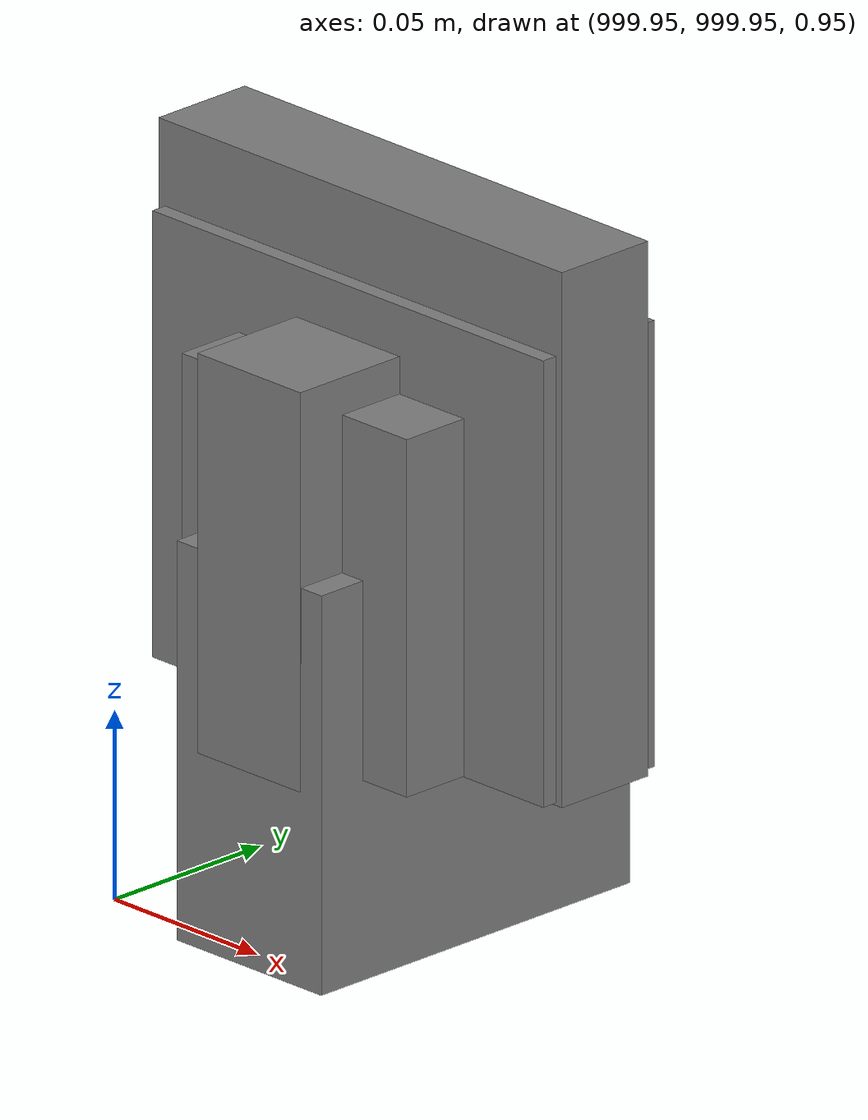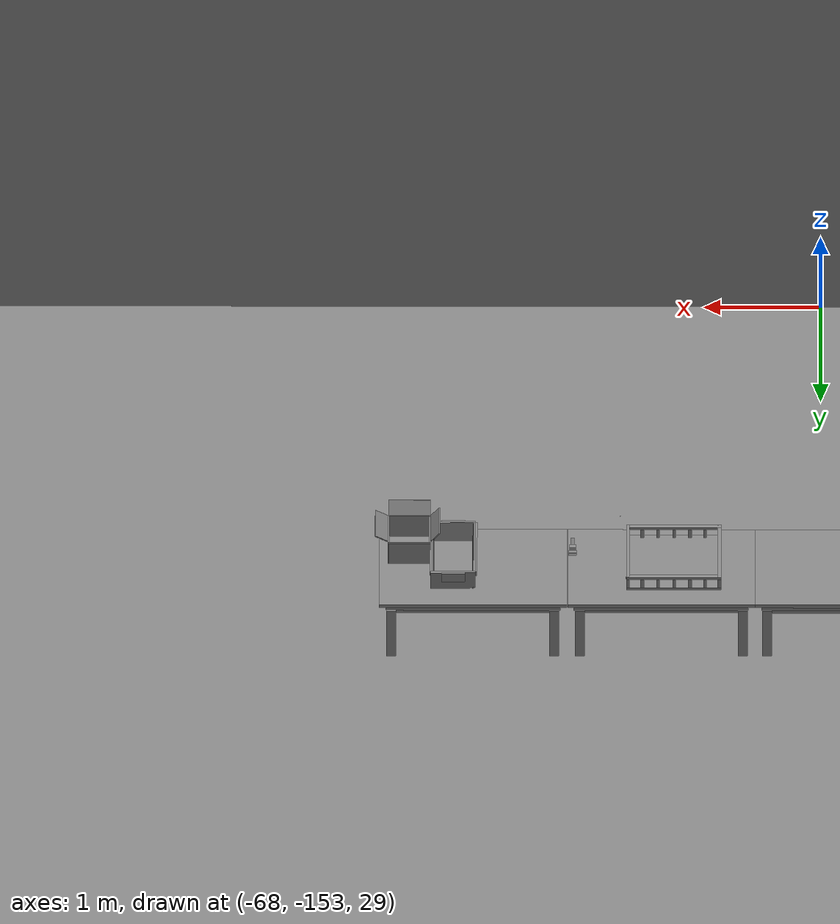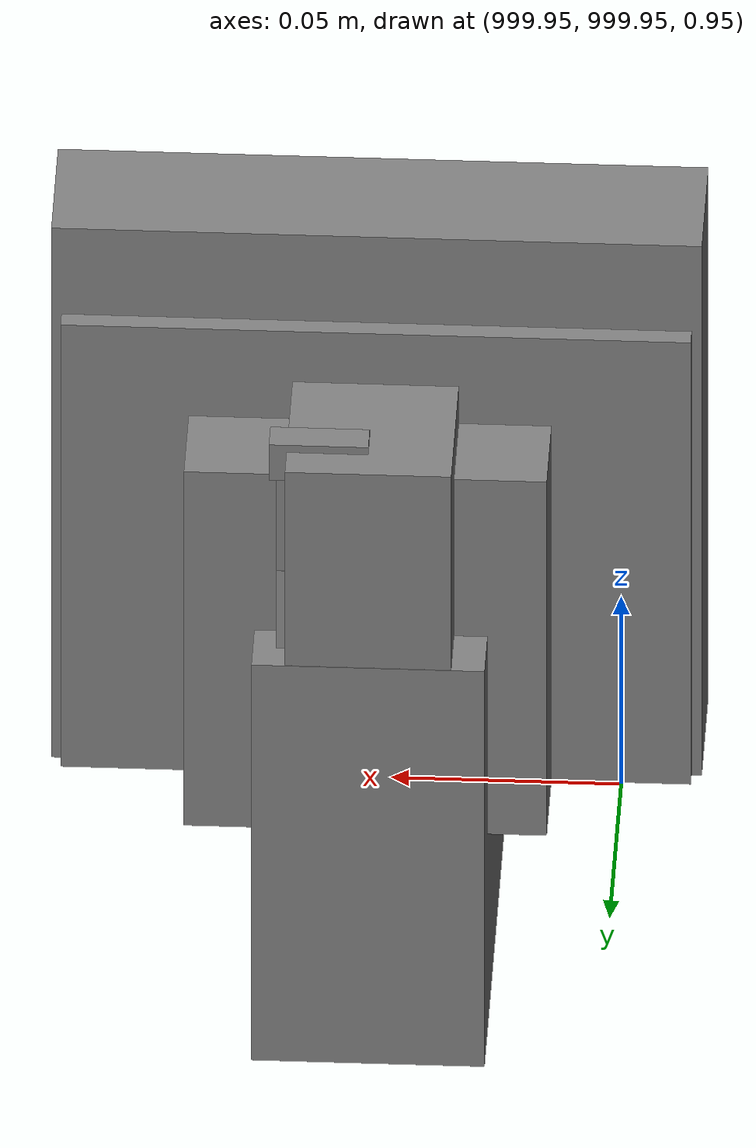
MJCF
<mujoco>
    <option gravity="0.000000000 0.000000000 -9.810000420" timestep="0.0049999999" integrator="implicitfast" density="1.225" viscosity="1.8000001e-05" noslip_iterations="10" iterations="100" sdf_iterations="50">
        <flag multiccd="disable"/>
    </option>
    <size memory="1000M"/>
    <compiler coordinate="local"/>
    <worldbody>
        <light cutoff="30" pos="0 1 1" dir="0 -1 -2"/>
        <light cutoff="30" pos="0 -1 1" dir="0 1 -2"/>
        <body pos="-66.133857727 -148.923706055 31.163143158" euler="68.378021240 55.403125763 -148.933502197" mocap="true" name="spotlight3_SpotLight"/>
        <body pos="-66.048698425 -149.552154541 31.169967651" euler="-76.052833557 -42.710166931 2.192680120" mocap="true" name="spotlight5_SpotLight"/>
        <body pos="1000.000000000 1000.000000000 1.000000000" euler="0.000000000 0.000000000 180.000000000" name="openloong_gripper_2f85_fix_base_usda_cpu_fan">
            <geom contype="1" conaffinity="1" density="1000" type="box" material="" rgba="0.500000000 0.500000000 0.500000000 1.000000000" solimp="0.899999976 0.949999988 0.001000000" friction="1.000000000 0.005000000 0.000100000" solref="0.020000000 1.000000000" margin="0" condim="3" group="0" pos="0.000000000 0.000000000 0.070034981" quat="0.000000000 0.000000000 0.000000000 1.000000000" size="0.070700005 0.014699999 0.070700005" name="openloong_gripper_2f85_fix_base_usda_geom_C249CF50_CB57_48CA_8E54_C4B975310C90"/>
            <freejoint name="openloong_gripper_2f85_fix_base_usda_cpu_fan_joint"/>
            <site size="0.005000000 0.005000000 0.005000000" rgba="0.500000000 0.500000000 0.500000000 1.000000000" pos="0.000000000 0.000000000 0.000000000" quat="0.999961913 0.008726535 0.000000000 0.000000000" group="0" type="sphere" name="openloong_gripper_2f85_fix_base_usda_cpu_fancsite"/>
        </body>
        <body pos="1000.000000000 1000.000000000 1.000000000" euler="0.000000000 0.000000000 180.000000000" name="openloong_gripper_2f85_fix_base_usda_wifi_box">
            <geom contype="1" conaffinity="1" density="1000" type="box" material="" rgba="0.500000000 0.500000000 0.500000000 1.000000000" solimp="0.899999976 0.949999988 0.001000000" friction="1.000000000 0.005000000 0.000100000" solref="0.020000000 1.000000000" margin="0" condim="3" group="0" pos="0.000000000 0.000000000 0.058978677" quat="0.000000000 0.000000047 0.000000000 1.000000000" size="0.068499997 0.018999999 0.059000000" name="openloong_gripper_2f85_fix_base_usda_geom_67A972FA_625B_4CBD_9BD3_920C8E1648F2"/>
            <freejoint name="openloong_gripper_2f85_fix_base_usda_wifi_box_joint"/>
            <site size="0.005000000 0.005000000 0.005000000" rgba="0.500000000 0.500000000 0.500000000 1.000000000" pos="0.000000000 0.000000000 0.000000000" quat="0.999961913 0.008726500 0.000000000 0.000000000" group="0" type="sphere" name="openloong_gripper_2f85_fix_base_usda_wifi_boxsite"/>
        </body>
        <body pos="1000.000000000 1000.000000000 1.000000000" euler="0.000011953 0.000005123 -179.999984741" name="openloong_gripper_2f85_fix_base_usda_intel_box">
            <geom contype="1" conaffinity="1" density="1000" type="box" material="" rgba="0.500000000 0.500000000 0.500000000 1.000000000" solimp="0.899999976 0.949999988 0.001000000" friction="1.000000000 0.005000000 0.000100000" solref="0.020000000 1.000000000" margin="0" condim="3" group="0" pos="0.000000000 -0.000067139 0.000082284" quat="0.707106709 0.000000225 0.000000253 0.707106650" size="0.052800003 0.025300000 0.052800003" name="openloong_gripper_2f85_fix_base_usda_geom_7EC90F47_4707_4FB1_A7D1_70EA8004DA5B"/>
            <freejoint name="openloong_gripper_2f85_fix_base_usda_intel_box_joint"/>
            <site size="0.005000000 0.005000000 0.005000000" rgba="0.500000000 0.500000000 0.500000000 1.000000000" pos="0.000000000 0.000000000 0.000000000" quat="0.999961913 0.008726500 0.000000000 0.000000000" group="0" type="sphere" name="openloong_gripper_2f85_fix_base_usda_intel_boxsite"/>
        </body>
        <body pos="1000.000000000 999.999938965 1.000000000" euler="0.000000000 0.000000000 180.000000000" name="openloong_gripper_2f85_fix_base_usda_intelcore_i5">
            <geom contype="1" conaffinity="1" density="1000" type="box" material="" rgba="0.500000000 0.500000000 0.500000000 1.000000000" solimp="0.899999976 0.949999988 0.001000000" friction="1.000000000 0.005000000 0.000100000" solref="0.020000000 1.000000000" margin="0" condim="3" group="0" pos="0.000000000 0.000000000 0.051722717" quat="0.707106709 0.000000000 0.000000000 -0.707106769" size="0.052800000 0.018080002 0.052800000" name="openloong_gripper_2f85_fix_base_usda_geom_BE2077DC_160C_4B6B_90EE_1F50BFFA0F41"/>
            <freejoint name="openloong_gripper_2f85_fix_base_usda_intelcore_i5_joint"/>
            <site size="0.005000000 0.005000000 0.005000000" rgba="0.500000000 0.500000000 0.500000000 1.000000000" pos="0.000000000 0.000000000 0.000000000" quat="0.999961913 0.008726534 0.000000000 0.000000000" group="0" type="sphere" name="openloong_gripper_2f85_fix_base_usda_intelcore_i5site"/>
        </body>
        <body pos="1000.000000000 1000.000000000 1.000000000" euler="0.000000000 0.000000000 180.000000000" name="openloong_gripper_2f85_fix_base_usda_battery_01">
            <geom contype="1" conaffinity="1" density="1000" type="box" material="" rgba="0.500000000 0.500000000 0.500000000 1.000000000" solimp="0.899999976 0.949999988 0.001000000" friction="1.000000000 0.005000000 0.000100000" solref="0.020000000 1.000000000" margin="0" condim="3" group="0" pos="-0.011123657 -0.041940309 0.101691343" quat="1.000000000 0.000000000 0.000000000 0.000000000" size="0.010800000 0.003375000 0.004725000" name="openloong_gripper_2f85_fix_base_usda_geom_D0651104_E2BA_4AC0_A762_E800B45597F0"/>
            <geom contype="1" conaffinity="1" density="1000" type="box" material="" rgba="0.500000000 0.500000000 0.500000000 1.000000000" solimp="0.899999976 0.949999988 0.001000000" friction="1.000000000 0.005000000 0.000100000" solref="0.020000000 1.000000000" margin="0" condim="3" group="0" pos="-0.010876465 -0.044247437 0.047066893" quat="0.998702705 -0.050920475 0.000000000 0.000000000" size="0.009450001 0.002700000 0.024975000" name="openloong_gripper_2f85_fix_base_usda_geom_418A60EF_4EB8_410D_8A48_9BCEF82DE086"/>
            <geom contype="1" conaffinity="1" density="1000" type="box" material="" rgba="0.500000000 0.500000000 0.500000000 1.000000000" solimp="0.899999976 0.949999988 0.001000000" friction="1.000000000 0.005000000 0.000100000" solref="0.020000000 1.000000000" margin="0" condim="3" group="0" pos="-0.001235962 -0.000659180 0.047381196" quat="1.000000000 0.000000000 0.000000000 0.000000000" size="0.039420001 0.039150000 0.047250003" name="openloong_gripper_2f85_fix_base_usda_geom_2BFFADC3_3EF8_46B2_BD48_92C2C4433B4D"/>
            <geom contype="1" conaffinity="1" density="1000" type="box" material="" rgba="0.500000000 0.500000000 0.500000000 1.000000000" solimp="0.899999976 0.949999988 0.001000000" friction="1.000000000 0.005000000 0.000100000" solref="0.020000000 1.000000000" margin="0" condim="3" group="0" pos="-0.010876465 -0.039138794 0.009851727" quat="1.000000000 0.000000000 0.000000000 0.000000000" size="0.009450001 0.010800000 0.013500000" name="openloong_gripper_2f85_fix_base_usda_geom_42853A28_1E1D_480C_8F9E_576B700C709A"/>
            <geom contype="1" conaffinity="1" density="1000" type="box" material="" rgba="0.500000000 0.500000000 0.500000000 1.000000000" solimp="0.899999976 0.949999988 0.001000000" friction="1.000000000 0.005000000 0.000100000" solref="0.020000000 1.000000000" margin="0" condim="3" group="0" pos="-0.010876465 -0.041528322 0.071508206" quat="1.000000000 0.000000000 0.000000000 0.000000000" size="0.009450001 0.002700000 0.027000001" name="openloong_gripper_2f85_fix_base_usda_geom_F865A7A9_1B54_4FCC_9878_FABF14E40077"/>
            <freejoint name="openloong_gripper_2f85_fix_base_usda_battery_01_joint"/>
            <site size="0.005000000 0.005000000 0.005000000" rgba="0.500000000 0.500000000 0.500000000 1.000000000" pos="0.000000000 0.000000000 0.000000000" quat="0.999961913 0.008726500 0.000000000 0.000000000" group="0" type="sphere" name="openloong_gripper_2f85_fix_base_usda_battery_01site"/>
        </body>
        <body pos="-66.357559204 -148.938659668 31.167415619" euler="87.059616089 -56.509567261 34.200550079" mocap="true" name="spotlight4_SpotLight"/>
        <body pos="-64.866622925 -149.383972168 30.183746338" euler="89.999984741 89.999946594 0.000000000" name="openloong_gripper_2f85_fix_base_usda_bluebox_01">
            <geom contype="1" conaffinity="1" density="1000" type="box" material="" rgba="0.500000000 0.500000000 0.500000000 1.000000000" solimp="0.899999976 0.949999988 0.001000000" friction="1.000000000 0.005000000 0.000100000" solref="0.020000000 1.000000000" margin="0" condim="3" group="0" pos="0.276580811 0.187225342 0.000068665" quat="0.707106948 0.000077471 0.707106352 0.000077486" size="0.100000001 0.057999998 0.010000000" name="openloong_gripper_2f85_fix_base_usda_geom_2A8A84BA_B22F_4744_998A_FDFCA13308A9"/>
            <geom contype="1" conaffinity="1" density="1000" type="box" material="" rgba="0.500000000 0.500000000 0.500000000 1.000000000" solimp="0.899999976 0.949999988 0.001000000" friction="1.000000000 0.005000000 0.000100000" solref="0.020000000 1.000000000" margin="0" condim="3" group="0" pos="0.000000000 0.002883911 0.000000000" quat="0.999999881 0.000000000 0.000000000 0.000000000" size="0.254000008 0.003000000 0.172000006" name="openloong_gripper_2f85_fix_base_usda_geom_AB56DF4C_3103_444F_A1E6_0B9AF206BFCF"/>
            <geom contype="1" conaffinity="1" density="1000" type="box" material="" rgba="0.500000000 0.500000000 0.500000000 1.000000000" solimp="0.899999976 0.949999988 0.001000000" friction="1.000000000 0.005000000 0.000100000" solref="0.020000000 1.000000000" margin="0" condim="3" group="0" pos="0.000000000 0.124874115 0.173484802" quat="0.999796331 0.020176515 -0.000000015 0.000000030" size="0.259999990 0.119999997 0.007000000" name="openloong_gripper_2f85_fix_base_usda_geom_E96948C6_F194_4D4C_8D49_DC09477F8893"/>
            <geom contype="1" conaffinity="1" density="1000" type="box" material="" rgba="0.500000000 0.500000000 0.500000000 1.000000000" solimp="0.899999976 0.949999988 0.001000000" friction="1.000000000 0.005000000 0.000100000" solref="0.020000000 1.000000000" margin="0" condim="3" group="0" pos="0.000000000 0.124874115 -0.173469543" quat="0.999796331 -0.020176545 -0.000000015 0.000000000" size="0.259999990 0.119999997 0.007000000" name="openloong_gripper_2f85_fix_base_usda_geom_E1F0887A_E115_4456_A76F_6181E6AC46E9"/>
            <geom contype="1" conaffinity="1" density="1000" type="box" material="" rgba="0.500000000 0.500000000 0.500000000 1.000000000" solimp="0.899999976 0.949999988 0.001000000" friction="1.000000000 0.005000000 0.000100000" solref="0.020000000 1.000000000" margin="0" condim="3" group="0" pos="0.000000000 0.214008331 0.188980103" quat="0.999912977 0.013176724 0.000000015 0.000000000" size="0.259999990 0.029999999 0.012500000" name="openloong_gripper_2f85_fix_base_usda_geom_70148A3B_A94E_40E1_B22B_9BF951EC0AB4"/>
            <geom contype="1" conaffinity="1" density="1000" type="box" material="" rgba="0.500000000 0.500000000 0.500000000 1.000000000" solimp="0.899999976 0.949999988 0.001000000" friction="1.000000000 0.005000000 0.000100000" solref="0.020000000 1.000000000" margin="0" condim="3" group="0" pos="-0.258361816 0.125289917 0.001876831" quat="0.702796936 -0.020792112 0.710783124 0.020769298" size="0.189999998 0.119999997 0.009000000" name="openloong_gripper_2f85_fix_base_usda_geom_C2F6E7FB_99E4_4C80_8B51_7EF87E6FC776"/>
            <geom contype="1" conaffinity="1" density="1000" type="box" material="" rgba="0.500000000 0.500000000 0.500000000 1.000000000" solimp="0.899999976 0.949999988 0.001000000" friction="1.000000000 0.005000000 0.000100000" solref="0.020000000 1.000000000" margin="0" condim="3" group="0" pos="0.000000000 0.214008331 -0.188980103" quat="0.999912977 -0.013176769 0.000000030 0.000000015" size="0.259999990 0.029999999 0.012500000" name="openloong_gripper_2f85_fix_base_usda_geom_EE76B28E_ED05_4D15_9C50_7EF9927C2A37"/>
            <geom contype="1" conaffinity="1" density="1000" type="box" material="" rgba="0.500000000 0.500000000 0.500000000 1.000000000" solimp="0.899999976 0.949999988 0.001000000" friction="1.000000000 0.005000000 0.000100000" solref="0.020000000 1.000000000" margin="0" condim="3" group="0" pos="-0.276611328 0.187225342 0.000068665" quat="0.707106650 0.000077441 0.707106709 0.000077456" size="0.100000001 0.057999998 0.010000000" name="openloong_gripper_2f85_fix_base_usda_geom_5AEB4E2A_34AF_4326_AF69_79000EA2D98D"/>
            <geom contype="1" conaffinity="1" density="1000" type="box" material="" rgba="0.500000000 0.500000000 0.500000000 1.000000000" solimp="0.899999976 0.949999988 0.001000000" friction="1.000000000 0.005000000 0.000100000" solref="0.020000000 1.000000000" margin="0" condim="3" group="0" pos="0.258331299 0.125289917 0.001876831" quat="0.702851415 0.018856421 0.710823774 -0.019329369" size="0.189999998 0.119999997 0.009000000" name="openloong_gripper_2f85_fix_base_usda_geom_A1545E0C_4754_49E3_825C_4821B98F7477"/>
            <freejoint name="openloong_gripper_2f85_fix_base_usda_bluebox_01_joint"/>
            <site size="0.005000000 0.005000000 0.005000000" rgba="0.500000000 0.500000000 0.500000000 1.000000000" pos="0.000000000 0.000000000 0.000000000" quat="0.999961913 0.008726534 0.000000000 0.000000000" group="0" type="sphere" name="openloong_gripper_2f85_fix_base_usda_bluebox_01site"/>
        </body>
        <body pos="-64.496299744 -149.491867065 30.235729218" euler="0.000000000 0.000000000 89.999946594" name="openloong_gripper_2f85_fix_base_usda_cardboardbox_01">
            <geom contype="1" conaffinity="1" density="1000" type="box" material="" rgba="0.500000000 0.500000000 0.500000000 1.000000000" solimp="0.899999976 0.949999988 0.001000000" friction="1.000000000 0.005000000 0.000100000" solref="0.020000000 1.000000000" margin="0" condim="3" group="0" pos="-0.003166199 -0.004086494 0.005052090" quat="1.000000000 0.000000000 0.000000000 0.000000000" size="0.142499998 0.177500010 0.005000000" name="openloong_gripper_2f85_fix_base_usda_geom_80BD3DDA_1E87_4792_84E4_E2DF6C7267F1"/>
            <geom contype="1" conaffinity="1" density="1000" type="box" material="" rgba="0.500000000 0.500000000 0.500000000 1.000000000" solimp="0.899999976 0.949999988 0.001000000" friction="1.000000000 0.005000000 0.000100000" solref="0.020000000 1.000000000" margin="0" condim="3" group="0" pos="-0.003166199 0.170316696 0.150570869" quat="1.000000000 0.000000000 0.000000000 0.000000000" size="0.142499998 0.005000000 0.149999991" name="openloong_gripper_2f85_fix_base_usda_geom_90ADBC0C_C0D5_4AA1_9500_BB673B5887F8"/>
            <geom contype="1" conaffinity="1" density="1000" type="box" material="" rgba="0.500000000 0.500000000 0.500000000 1.000000000" solimp="0.899999976 0.949999988 0.001000000" friction="1.000000000 0.005000000 0.000100000" solref="0.020000000 1.000000000" margin="0" condim="3" group="0" pos="-0.147399902 -0.005307198 0.150570869" quat="1.000000000 0.000000000 0.000000000 0.000000000" size="0.005000000 0.177500010 0.149999991" name="openloong_gripper_2f85_fix_base_usda_geom_5E6E3D8C_5C68_4BB7_A385_F0E1F74CB684"/>
            <geom contype="1" conaffinity="1" density="1000" type="box" material="" rgba="0.500000000 0.500000000 0.500000000 1.000000000" solimp="0.899999976 0.949999988 0.001000000" friction="1.000000000 0.005000000 0.000100000" solref="0.020000000 1.000000000" margin="0" condim="3" group="0" pos="0.140275955 -0.005307198 0.150570869" quat="1.000000000 0.000000000 0.000000000 0.000000000" size="0.005000000 0.177500010 0.149999991" name="openloong_gripper_2f85_fix_base_usda_geom_D9737053_8894_46FE_BB4F_4A6798AB7FF8"/>
            <geom contype="1" conaffinity="1" density="1000" type="box" material="" rgba="0.500000000 0.500000000 0.500000000 1.000000000" solimp="0.899999976 0.949999988 0.001000000" friction="1.000000000 0.005000000 0.000100000" solref="0.020000000 1.000000000" margin="0" condim="3" group="0" pos="-0.003166199 -0.181550980 0.150570869" quat="1.000000000 0.000000000 0.000000000 0.000000000" size="0.142499998 0.005000000 0.149999991" name="openloong_gripper_2f85_fix_base_usda_geom_43BFB04E_49A7_42F7_85E4_D4D8C9F80F55"/>
            <freejoint name="openloong_gripper_2f85_fix_base_usda_cardboardbox_01_joint"/>
            <site size="0.005000000 0.005000000 0.005000000" rgba="0.500000000 0.500000000 0.500000000 1.000000000" pos="0.000000000 0.000000000 0.000000000" quat="0.999961913 0.008726535 0.000000000 0.000000000" group="0" type="sphere" name="openloong_gripper_2f85_fix_base_usda_site_046092E7_47CC_4E85_9615_81F75DDEBFCD"/>
            <body pos="0.139160156 -0.004048347 0.301930904" euler="-179.999954224 49.383502960 179.999954224" name="openloong_gripper_2f85_fix_base_usda_A1_006">
                <geom contype="1" conaffinity="1" density="1000" type="box" material="" rgba="0.500000000 0.500000000 0.500000000 1.000000000" solimp="0.899999976 0.949999988 0.001000000" friction="1.000000000 0.005000000 0.000100000" solref="0.020000000 1.000000000" margin="0" condim="3" group="0" pos="-0.071587563 0.000009537 0.001745224" quat="0.999999881 0.000000000 0.000000000 0.000000000" size="0.071249999 0.179999992 0.002500000" name="openloong_gripper_2f85_fix_base_usda_geom_E58011DB_7CD5_47C6_B44D_6BF3F5BC5060"/>
                <joint armature="0" stiffness="0.07" damping="0.0099999998" axis="0.000000 1.000000 0.000000" type="hinge" name="openloong_gripper_2f85_fix_base_usda_A1_006"/>
            </body>
            <body pos="-0.145902634 -0.004086494 0.301938057" euler="-180.000000000 -60.000011444 -180.000000000" name="openloong_gripper_2f85_fix_base_usda_A2_006">
                <geom contype="1" conaffinity="1" density="1000" type="box" material="" rgba="0.500000000 0.500000000 0.500000000 1.000000000" solimp="0.899999976 0.949999988 0.001000000" friction="1.000000000 0.005000000 0.000100000" solref="0.020000000 1.000000000" margin="0" condim="3" group="0" pos="0.071268082 0.000009537 0.002717972" quat="0.000002921 0.000000000 -0.000000030 0.999999881" size="0.071249999 0.179999992 0.002500000" name="openloong_gripper_2f85_fix_base_usda_geom_4165EE3E_5E2A_471C_820A_582B4E5409D9"/>
                <joint armature="0" stiffness="0.07" damping="0.0099999998" axis="0.000000 1.000000 0.000000" type="hinge" name="openloong_gripper_2f85_fix_base_usda_A2_006"/>
            </body>
            <body pos="-0.003385544 0.175991058 0.301930904" euler="-125.858116150 -0.000004561 0.000002331" name="openloong_gripper_2f85_fix_base_usda_B2_006">
                <geom contype="1" conaffinity="1" density="1000" type="box" material="" rgba="0.500000000 0.500000000 0.500000000 1.000000000" solimp="0.899999976 0.949999988 0.001000000" friction="1.000000000 0.005000000 0.000100000" solref="0.020000000 1.000000000" margin="0" condim="3" group="0" pos="0.000009537 -0.070939064 -0.002470016" quat="0.999614120 0.027776197 -0.000000015 0.000000030" size="0.137500003 0.064999998 0.005000000" name="openloong_gripper_2f85_fix_base_usda_geom_F653A3A9_0D0A_4F1C_96EB_BA524560F6A1"/>
                <joint armature="0" stiffness="0.07" damping="0.0099999998" axis="1.000000 0.000000 0.000000" type="hinge" name="openloong_gripper_2f85_fix_base_usda_B2_006"/>
            </body>
            <body pos="-0.003385544 -0.184140205 0.301938057" euler="147.805557251 0.000000000 0.000000000" name="openloong_gripper_2f85_fix_base_usda_B1_006">
                <geom contype="1" conaffinity="1" density="1000" type="box" material="" rgba="0.500000000 0.500000000 0.500000000 1.000000000" solimp="0.899999976 0.949999988 0.001000000" friction="1.000000000 0.005000000 0.000100000" solref="0.020000000 1.000000000" margin="0" condim="3" group="0" pos="-0.000028610 0.070202351 -0.002703667" quat="0.999614179 -0.027776167 0.000000000 0.000000000" size="0.137500003 0.064999998 0.005000000" name="openloong_gripper_2f85_fix_base_usda_geom_67606064_6B58_43E6_86CA_3329CB9E6675"/>
                <joint armature="0" stiffness="0.07" damping="0.0099999998" axis="1.000000 0.000000 0.000000" type="hinge" name="openloong_gripper_2f85_fix_base_usda_B1_006"/>
            </body>
        </body>
        <body pos="-65.882858276 -149.481979370 30.229999542" euler="-64.487716675 0.000000000 0.000000000" name="openloong_gripper_2f85_fix_base_usda_Barcode">
            <geom contype="1" conaffinity="1" density="1000" type="box" material="" rgba="0.500000000 0.500000000 0.500000000 1.000000000" solimp="0.899999976 0.949999988 0.001000000" friction="1.000000000 0.005000000 0.000100000" solref="0.020000000 1.000000000" margin="0" condim="3" group="0" pos="0.000000000 0.013038635 0.001419067" quat="0.000000000 0.000000000 0.000000000 1.000000119" size="0.034000002 0.010000000 0.017999999" name="openloong_gripper_2f85_fix_base_usda_geom_8C0FBF6C_380B_45F4_A6B0_A181C9C8CECA"/>
            <geom contype="1" conaffinity="1" density="1000" type="box" material="" rgba="0.500000000 0.500000000 0.500000000 1.000000000" solimp="0.899999976 0.949999988 0.001000000" friction="1.000000000 0.005000000 0.000100000" solref="0.020000000 1.000000000" margin="0" condim="3" group="0" pos="0.000000000 -0.035301208 -0.007095337" quat="0.000000000 0.000000000 -0.043619365 0.999048233" size="0.028999999 0.010000000 0.020000000" name="openloong_gripper_2f85_fix_base_usda_geom_5733C953_9AD6_4D36_BE7D_6203915310E9"/>
            <geom contype="1" conaffinity="1" density="1000" type="box" material="" rgba="0.500000000 0.500000000 0.500000000 1.000000000" solimp="0.899999976 0.949999988 0.001000000" friction="1.000000000 0.005000000 0.000100000" solref="0.020000000 1.000000000" margin="0" condim="3" group="0" pos="0.000000000 -0.043411255 -0.011749268" quat="0.922262907 0.386563420 0.000000000 0.000000000" size="0.026000001 0.010000000 0.020000000" name="openloong_gripper_2f85_fix_base_usda_geom_BBE7A9FD_CECF_49B2_8FD6_2686C4B150DE"/>
            <geom contype="1" conaffinity="1" density="1000" type="box" material="" rgba="0.500000000 0.500000000 0.500000000 1.000000000" solimp="0.899999976 0.949999988 0.001000000" friction="1.000000000 0.005000000 0.000100000" solref="0.020000000 1.000000000" margin="0" condim="3" group="0" pos="0.000000000 -0.016967773 -0.031860352" quat="0.000000000 0.000000000 0.000000000 1.000000119" size="0.008000000 0.010000000 0.013000000" name="openloong_gripper_2f85_fix_base_usda_geom_395D072D_FA38_4521_984F_D2D228C11E11"/>
            <geom contype="1" conaffinity="1" density="1000" type="box" material="" rgba="0.500000000 0.500000000 0.500000000 1.000000000" solimp="0.899999976 0.949999988 0.001000000" friction="1.000000000 0.005000000 0.000100000" solref="0.020000000 1.000000000" margin="0" condim="3" group="0" pos="0.000000000 -0.001869202 0.000312805" quat="0.953716993 0.300705761 0.000000000 0.000000000" size="0.032000002 0.010000000 0.018999999" name="openloong_gripper_2f85_fix_base_usda_geom_2EF11D7B_A660_469A_A8EF_2AB3EF8F05D6"/>
            <geom contype="1" conaffinity="1" density="1000" type="box" material="" rgba="0.500000000 0.500000000 0.500000000 1.000000000" solimp="0.899999976 0.949999988 0.001000000" friction="1.000000000 0.005000000 0.000100000" solref="0.020000000 1.000000000" margin="0" condim="3" group="0" pos="0.000000000 -0.019531250 -0.003173828" quat="0.953716993 0.300705761 0.000000000 0.000000000" size="0.030999999 0.010000000 0.020000000" name="openloong_gripper_2f85_fix_base_usda_geom_3FA5723A_B30D_43E1_AF41_93A1EF05B202"/>
            <geom contype="1" conaffinity="1" density="1000" type="box" material="" rgba="0.500000000 0.500000000 0.500000000 1.000000000" solimp="0.899999976 0.949999988 0.001000000" friction="1.000000000 0.005000000 0.000100000" solref="0.020000000 1.000000000" margin="0" condim="3" group="0" pos="0.000000000 -0.035301208 -0.007095337" quat="0.953716993 0.300705761 0.000000000 0.000000000" size="0.028999999 0.010000000 0.020000000" name="openloong_gripper_2f85_fix_base_usda_geom_2D7D682B_B0C3_408E_845D_F434DB4F4DD3"/>
            <geom contype="1" conaffinity="1" density="1000" type="box" material="" rgba="0.500000000 0.500000000 0.500000000 1.000000000" solimp="0.899999976 0.949999988 0.001000000" friction="1.000000000 0.005000000 0.000100000" solref="0.020000000 1.000000000" margin="0" condim="3" group="0" pos="0.000000000 -0.042617798 -0.071121216" quat="0.000000000 0.000000000 0.000000000 1.000000119" size="0.013000000 0.021000000 0.059999999" name="openloong_gripper_2f85_fix_base_usda_geom_45A48338_085C_4C53_8906_CD3579EAF469"/>
            <freejoint name="openloong_gripper_2f85_fix_base_usda_Barcode_joint"/>
            <site size="0.005000000 0.005000000 0.005000000" rgba="0.500000000 0.500000000 0.500000000 1.000000000" pos="0.000000000 0.000000000 0.000000000" quat="1.000000000 0.000000000 0.000000000 0.000000000" group="0" type="sphere" name="openloong_gripper_2f85_fix_base_usda_Barcode_site"/>
        </body>
        <body pos="-66.745018005 -149.392349243 30.184000015" euler="0.000000000 0.000000000 89.999946594" name="[22330758609880]_Basket_01">
            <geom contype="1" conaffinity="1" density="1000" type="box" material="" rgba="0.500000000 0.500000000 0.500000000 1.000000000" solimp="0.899999976 0.949999988 0.001000000" friction="1.000000000 0.005000000 0.000100000" solref="0.020000000 1.000000000" margin="0" condim="3" group="0" pos="-0.052425385 0.389207840 0.089787483" quat="0.707107008 0.000000000 0.000000000 0.707106411" size="0.014249999 0.014249999 0.059999999" name="[22330758609880]_geom_199AD52A_B0E1_4473_810B_DC33CFC6A04C"/>
            <geom contype="1" conaffinity="1" density="1000" type="box" material="" rgba="0.500000000 0.500000000 0.500000000 1.000000000" solimp="0.899999976 0.949999988 0.001000000" friction="1.000000000 0.005000000 0.000100000" solref="0.020000000 1.000000000" margin="0" condim="3" group="0" pos="0.264015198 -0.133043289 0.089787483" quat="0.707107008 0.000000000 0.000000000 0.707106411" size="0.014249999 0.014249999 0.059999999" name="[22330758609880]_geom_3812BAE1_9AC3_4672_BFB5_0AB71D2544B0"/>
            <geom contype="1" conaffinity="1" density="1000" type="box" material="" rgba="0.500000000 0.500000000 0.500000000 1.000000000" solimp="0.899999976 0.949999988 0.001000000" friction="1.000000000 0.005000000 0.000100000" solref="0.020000000 1.000000000" margin="0" condim="3" group="0" pos="-0.264015198 -0.265548706 0.089793205" quat="0.707107008 0.000000000 0.000000000 0.707106411" size="0.014249999 0.014249999 0.059999999" name="[22330758609880]_geom_7781DDB5_ED87_49C6_B94E_16E2573C7127"/>
            <geom contype="1" conaffinity="1" density="1000" type="box" material="" rgba="0.500000000 0.500000000 0.500000000 1.000000000" solimp="0.899999976 0.949999988 0.001000000" friction="1.000000000 0.005000000 0.000100000" solref="0.020000000 1.000000000" margin="0" condim="3" group="0" pos="-0.160263062 -0.389322281 0.089793205" quat="0.707107008 0.000000000 0.000000000 0.707106411" size="0.014249999 0.014249999 0.059999999" name="[22330758609880]_geom_BBA6904E_6485_46F3_9AF9_B23A65B4FF5F"/>
            <geom contype="1" conaffinity="1" density="1000" type="box" material="" rgba="0.500000000 0.500000000 0.500000000 1.000000000" solimp="0.899999976 0.949999988 0.001000000" friction="1.000000000 0.005000000 0.000100000" solref="0.020000000 1.000000000" margin="0" condim="3" group="0" pos="0.162265778 -0.389322281 0.089787483" quat="0.707107008 0.000000000 0.000000000 0.707106411" size="0.014249999 0.014249999 0.059999999" name="[22330758609880]_geom_82A0767D_361B_48D6_8BB4_C480B7F8FB5B"/>
            <geom contype="1" conaffinity="1" density="1000" type="box" material="" rgba="0.500000000 0.500000000 0.500000000 1.000000000" solimp="0.899999976 0.949999988 0.001000000" friction="1.000000000 0.005000000 0.000100000" solref="0.020000000 1.000000000" margin="0" condim="3" group="0" pos="0.264015198 0.389207840 0.089787483" quat="0.707107008 0.000000000 0.000000000 0.707106411" size="0.014249999 0.014249999 0.059999999" name="[22330758609880]_geom_551A02EA_AC96_4ADD_AAEC_E0B95279B472"/>
            <geom contype="1" conaffinity="1" density="1000" type="box" material="" rgba="0.500000000 0.500000000 0.500000000 1.000000000" solimp="0.899999976 0.949999988 0.001000000" friction="1.000000000 0.005000000 0.000100000" solref="0.020000000 1.000000000" margin="0" condim="3" group="0" pos="-0.264015198 -0.133043289 0.089793205" quat="0.707107008 0.000000000 0.000000000 0.707106411" size="0.014249999 0.014249999 0.059999999" name="[22330758609880]_geom_3C604F4E_37CD_46EC_B5CF_D7CD7D6F85ED"/>
            <geom contype="1" conaffinity="1" density="1000" type="box" material="" rgba="0.500000000 0.500000000 0.500000000 1.000000000" solimp="0.899999976 0.949999988 0.001000000" friction="1.000000000 0.005000000 0.000100000" solref="0.020000000 1.000000000" margin="0" condim="3" group="0" pos="-0.264026642 0.269256592 0.089793205" quat="0.707107008 0.000000000 0.000000000 0.707106411" size="0.014249999 0.014249999 0.059999999" name="[22330758609880]_geom_0FBF7E65_8B9C_454E_986D_B1782EB8E5B9"/>
            <geom contype="1" conaffinity="1" density="1000" type="box" material="" rgba="0.500000000 0.500000000 0.500000000 1.000000000" solimp="0.899999976 0.949999988 0.001000000" friction="1.000000000 0.005000000 0.000100000" solref="0.020000000 1.000000000" margin="0" condim="3" group="0" pos="0.054462433 0.389207840 0.089787483" quat="0.707107008 0.000000000 0.000000000 0.707106411" size="0.014249999 0.014249999 0.059999999" name="[22330758609880]_geom_5A369449_0E40_4C4A_BAC1_B25D8E61C1F0"/>
            <geom contype="1" conaffinity="1" density="1000" type="box" material="" rgba="0.500000000 0.500000000 0.500000000 1.000000000" solimp="0.899999976 0.949999988 0.001000000" friction="1.000000000 0.005000000 0.000100000" solref="0.020000000 1.000000000" margin="0" condim="3" group="0" pos="0.054462433 -0.389322281 0.089787483" quat="0.707107008 0.000000000 0.000000000 0.707106411" size="0.014249999 0.014249999 0.059999999" name="[22330758609880]_geom_5637AB2E_5D0B_4C4E_9D4A_C1B340DFC854"/>
            <geom contype="1" conaffinity="1" density="1000" type="box" material="" rgba="0.500000000 0.500000000 0.500000000 1.000000000" solimp="0.899999976 0.949999988 0.001000000" friction="1.000000000 0.005000000 0.000100000" solref="0.020000000 1.000000000" margin="0" condim="3" group="0" pos="0.264015198 0.269256592 0.089793205" quat="0.707107008 0.000000000 0.000000000 0.707106411" size="0.014249999 0.014249999 0.059999999" name="[22330758609880]_geom_5B879656_C2F4_4A36_B56D_C54736640F66"/>
            <geom contype="1" conaffinity="1" density="1000" type="box" material="" rgba="0.500000000 0.500000000 0.500000000 1.000000000" solimp="0.899999976 0.949999988 0.001000000" friction="1.000000000 0.005000000 0.000100000" solref="0.020000000 1.000000000" margin="0" condim="3" group="0" pos="0.264015198 -0.389322281 0.089787483" quat="0.707107008 0.000000000 0.000000000 0.707106411" size="0.014249999 0.014249999 0.059999999" name="[22330758609880]_geom_8F31204C_8A41_462F_AABF_931CC515E150"/>
            <geom contype="1" conaffinity="1" density="1000" type="box" material="" rgba="0.500000000 0.500000000 0.500000000 1.000000000" solimp="0.899999976 0.949999988 0.001000000" friction="1.000000000 0.005000000 0.000100000" solref="0.020000000 1.000000000" margin="0" condim="3" group="0" pos="0.000000000 0.000000000 0.015998840" quat="0.707107008 0.000000000 0.000000000 0.707106411" size="0.403499991 0.279000014 0.015750000" name="[22330758609880]_geom_BE6E6994_7AB7_4064_93D3_85CC870E88DB"/>
            <geom contype="1" conaffinity="1" density="1000" type="box" material="" rgba="0.500000000 0.500000000 0.500000000 1.000000000" solimp="0.899999976 0.949999988 0.001000000" friction="1.000000000 0.005000000 0.000100000" solref="0.020000000 1.000000000" margin="0" condim="3" group="0" pos="0.000000000 -0.389476776 0.163619041" quat="0.707107008 0.000000000 0.000000000 0.707106411" size="0.015000000 0.277500004 0.015750000" name="[22330758609880]_geom_777EA533_9BA0_4280_9360_B08C531B843A"/>
            <geom contype="1" conaffinity="1" density="1000" type="box" material="" rgba="0.500000000 0.500000000 0.500000000 1.000000000" solimp="0.899999976 0.949999988 0.001000000" friction="1.000000000 0.005000000 0.000100000" solref="0.020000000 1.000000000" margin="0" condim="3" group="0" pos="0.162265778 0.389207840 0.089787483" quat="0.707107008 0.000000000 0.000000000 0.707106411" size="0.014249999 0.014249999 0.059999999" name="[22330758609880]_geom_36056072_0AD5_4AEA_AA31_E587F2807653"/>
            <geom contype="1" conaffinity="1" density="1000" type="box" material="" rgba="0.500000000 0.500000000 0.500000000 1.000000000" solimp="0.899999976 0.949999988 0.001000000" friction="1.000000000 0.005000000 0.000100000" solref="0.020000000 1.000000000" margin="0" condim="3" group="0" pos="0.000000000 0.389471054 0.163619041" quat="0.707107008 0.000000000 0.000000000 0.707106411" size="0.015000000 0.277500004 0.015750000" name="[22330758609880]_geom_94C95ED9_9B48_4F4B_A8F1_CED1AC89FA65"/>
            <geom contype="1" conaffinity="1" density="1000" type="box" material="" rgba="0.500000000 0.500000000 0.500000000 1.000000000" solimp="0.899999976 0.949999988 0.001000000" friction="1.000000000 0.005000000 0.000100000" solref="0.020000000 1.000000000" margin="0" condim="3" group="0" pos="-0.263511658 0.000000000 0.163619041" quat="0.707107008 0.000000000 0.000000000 0.707106411" size="0.403499991 0.015000000 0.015750000" name="[22330758609880]_geom_8E54D410_9F22_4751_9656_FA4DFCEF0A5C"/>
            <geom contype="1" conaffinity="1" density="1000" type="box" material="" rgba="0.500000000 0.500000000 0.500000000 1.000000000" solimp="0.899999976 0.949999988 0.001000000" friction="1.000000000 0.005000000 0.000100000" solref="0.020000000 1.000000000" margin="0" condim="3" group="0" pos="-0.264015198 0.141334534 0.089793205" quat="0.707107008 0.000000000 0.000000000 0.707106411" size="0.014249999 0.014249999 0.059999999" name="[22330758609880]_geom_12AAC508_0B53_4459_A01D_38AA35A7A5B6"/>
            <geom contype="1" conaffinity="1" density="1000" type="box" material="" rgba="0.500000000 0.500000000 0.500000000 1.000000000" solimp="0.899999976 0.949999988 0.001000000" friction="1.000000000 0.005000000 0.000100000" solref="0.020000000 1.000000000" margin="0" condim="3" group="0" pos="0.264015198 -0.265548706 0.089787483" quat="0.707107008 0.000000000 0.000000000 0.707106411" size="0.014249999 0.014249999 0.059999999" name="[22330758609880]_geom_07F649CA_F0AE_4A13_BD31_A6D439CD6651"/>
            <geom contype="1" conaffinity="1" density="1000" type="box" material="" rgba="0.500000000 0.500000000 0.500000000 1.000000000" solimp="0.899999976 0.949999988 0.001000000" friction="1.000000000 0.005000000 0.000100000" solref="0.020000000 1.000000000" margin="0" condim="3" group="0" pos="-0.160263062 0.389207840 0.089787483" quat="0.707107008 0.000000000 0.000000000 0.707106411" size="0.014249999 0.014249999 0.059999999" name="[22330758609880]_geom_F36C444B_9350_4A71_8D81_DA983692FE46"/>
            <geom contype="1" conaffinity="1" density="1000" type="box" material="" rgba="0.500000000 0.500000000 0.500000000 1.000000000" solimp="0.899999976 0.949999988 0.001000000" friction="1.000000000 0.005000000 0.000100000" solref="0.020000000 1.000000000" margin="0" condim="3" group="0" pos="-0.052425385 -0.389322281 0.089787483" quat="0.707107008 0.000000000 0.000000000 0.707106411" size="0.014249999 0.014249999 0.059999999" name="[22330758609880]_geom_423DFB41_2AF2_420D_B3AD_A2A5F2892EF3"/>
            <geom contype="1" conaffinity="1" density="1000" type="box" material="" rgba="0.500000000 0.500000000 0.500000000 1.000000000" solimp="0.899999976 0.949999988 0.001000000" friction="1.000000000 0.005000000 0.000100000" solref="0.020000000 1.000000000" margin="0" condim="3" group="0" pos="-0.264026642 -0.389322281 0.089793205" quat="0.707107008 0.000000000 0.000000000 0.707106411" size="0.014249999 0.014249999 0.059999999" name="[22330758609880]_geom_23498FC2_C45C_4C31_A2B9_476C678F306F"/>
            <geom contype="1" conaffinity="1" density="1000" type="box" material="" rgba="0.500000000 0.500000000 0.500000000 1.000000000" solimp="0.899999976 0.949999988 0.001000000" friction="1.000000000 0.005000000 0.000100000" solref="0.020000000 1.000000000" margin="0" condim="3" group="0" pos="0.264015198 0.141334534 0.089787483" quat="0.707107008 0.000000000 0.000000000 0.707106411" size="0.014249999 0.014249999 0.059999999" name="[22330758609880]_geom_8FD7592E_6C91_4002_BCE9_45C0D15BCFCB"/>
            <geom contype="1" conaffinity="1" density="1000" type="box" material="" rgba="0.500000000 0.500000000 0.500000000 1.000000000" solimp="0.899999976 0.949999988 0.001000000" friction="1.000000000 0.005000000 0.000100000" solref="0.020000000 1.000000000" margin="0" condim="3" group="0" pos="-0.264015198 0.389207840 0.089793205" quat="0.707107008 0.000000000 0.000000000 0.707106411" size="0.014249999 0.014249999 0.059999999" name="[22330758609880]_geom_A35F0CD6_FC45_4EA8_894A_7C67A5D7913E"/>
            <geom contype="1" conaffinity="1" density="1000" type="box" material="" rgba="0.500000000 0.500000000 0.500000000 1.000000000" solimp="0.899999976 0.949999988 0.001000000" friction="1.000000000 0.005000000 0.000100000" solref="0.020000000 1.000000000" margin="0" condim="3" group="0" pos="0.264015198 0.004480362 0.089787483" quat="0.707107008 0.000000000 0.000000000 0.707106411" size="0.014249999 0.014249999 0.059999999" name="[22330758609880]_geom_B8761A8C_41EA_4F64_B320_ECFEAD7AA173"/>
            <geom contype="1" conaffinity="1" density="1000" type="box" material="" rgba="0.500000000 0.500000000 0.500000000 1.000000000" solimp="0.899999976 0.949999988 0.001000000" friction="1.000000000 0.005000000 0.000100000" solref="0.020000000 1.000000000" margin="0" condim="3" group="0" pos="0.263694763 -0.000011444 0.163619041" quat="0.707107008 0.000000000 0.000000000 0.707106411" size="0.403499991 0.015000000 0.015750000" name="[22330758609880]_geom_D96999C5_5B93_4627_92E6_39BC93F2CA06"/>
            <geom contype="1" conaffinity="1" density="1000" type="box" material="" rgba="0.500000000 0.500000000 0.500000000 1.000000000" solimp="0.899999976 0.949999988 0.001000000" friction="1.000000000 0.005000000 0.000100000" solref="0.020000000 1.000000000" margin="0" condim="3" group="0" pos="-0.264015198 0.004480362 0.089793205" quat="0.707107008 0.000000000 0.000000000 0.707106411" size="0.014249999 0.014249999 0.059999999" name="[22330758609880]_geom_79DA61B4_0202_43E2_9BB7_FD2B257CDC5C"/>
            <freejoint name="[22330758609880]_joint_7A1B29EF_3F23_48F9_A447_F16CDD7DB483"/>
        </body>
        <body pos="0.000000000 0.000000000 0.000000000" euler="0.000000000 0.000000000 0.000000000" name="Static Objects_Static Objects">
            <geom contype="1" conaffinity="1" density="1000" type="box" material="" rgba="0.500000000 0.500000000 0.500000000 1.000000000" solimp="0.899999976 0.949999988 0.001000000" friction="1.000000000 0.005000000 0.000100000" solref="0.020000000 1.000000000" margin="0" condim="3" group="0" pos="-67.544113159 -149.365814209 29.727830887" quat="0.500000417 0.499999970 0.499999553 0.499999970" size="0.381000012 0.319999993 0.041000001" name="Static Objects_geom_6B7E5F2E_62EC_4337_94AD_430F441384D9"/>
            <geom contype="1" conaffinity="1" density="1000" type="box" material="" rgba="0.500000000 0.500000000 0.500000000 1.000000000" solimp="0.899999976 0.949999988 0.001000000" friction="1.000000000 0.005000000 0.000100000" solref="0.020000000 1.000000000" margin="0" condim="3" group="0" pos="-68.239501953 -149.365814209 30.086868286" quat="0.500000417 0.499999970 0.499999553 0.499999970" size="0.370999992 0.039500002 0.745000005" name="Static Objects_geom_8C534B27_B5AB_4216_B5D2_0699AF95D18C"/>
            <geom contype="1" conaffinity="1" density="1000" type="box" material="" rgba="0.500000000 0.500000000 0.500000000 1.000000000" solimp="0.899999976 0.949999988 0.001000000" friction="1.000000000 0.005000000 0.000100000" solref="0.020000000 1.000000000" margin="0" condim="3" group="0" pos="-68.239501953 -149.365814209 30.147235870" quat="0.500000417 0.499999970 0.499999553 0.499999970" size="0.400000006 0.022000000 0.800000012" name="Static Objects_geom_53FE8F5D_EBEA_45FB_AE71_D466BF70411C"/>
            <geom contype="1" conaffinity="1" density="1000" type="box" material="" rgba="0.500000000 0.500000000 0.500000000 1.000000000" solimp="0.899999976 0.949999988 0.001000000" friction="1.000000000 0.005000000 0.000100000" solref="0.020000000 1.000000000" margin="0" condim="3" group="0" pos="-68.934890747 -149.365814209 29.727830887" quat="0.500000417 0.499999970 0.499999553 0.499999970" size="0.381000012 0.319999993 0.041000001" name="Static Objects_geom_8BD5685B_F1BC_4D62_B52B_05F0B3C585C4"/>
            <geom contype="1" conaffinity="1" density="1000" type="box" material="" rgba="0.500000000 0.500000000 0.500000000 1.000000000" solimp="0.899999976 0.949999988 0.001000000" friction="1.000000000 0.005000000 0.000100000" solref="0.020000000 1.000000000" margin="0" condim="3" group="0" pos="-68.239501953 -149.365814209 29.561563492" quat="0.500000417 0.499999970 0.499999553 0.499999970" size="0.020000000 0.022000000 0.660000026" name="Static Objects_geom_6C90B37D_5D38_4211_9798_BC08D5E48A52"/>
            <geom contype="1" conaffinity="1" density="1000" type="box" material="" rgba="0.500000000 0.500000000 0.500000000 1.000000000" solimp="0.899999976 0.949999988 0.001000000" friction="1.000000000 0.005000000 0.000100000" solref="0.020000000 1.000000000" margin="0" condim="3" group="0" pos="-65.945671082 -149.365814209 29.727830887" quat="0.500000417 0.499999970 0.499999553 0.499999970" size="0.381000012 0.319999993 0.041000001" name="Static Objects_geom_E277C4A3_DE4D_4137_A1A9_5A8D4B62AA2D"/>
            <geom contype="1" conaffinity="1" density="1000" type="box" material="" rgba="0.500000000 0.500000000 0.500000000 1.000000000" solimp="0.899999976 0.949999988 0.001000000" friction="1.000000000 0.005000000 0.000100000" solref="0.020000000 1.000000000" margin="0" condim="3" group="0" pos="-66.641059875 -149.365814209 30.086868286" quat="0.500000417 0.499999970 0.499999553 0.499999970" size="0.370999992 0.039500002 0.745000005" name="Static Objects_geom_AAD476FD_8FBF_45C3_8329_712254637943"/>
            <geom contype="1" conaffinity="1" density="1000" type="box" material="" rgba="0.500000000 0.500000000 0.500000000 1.000000000" solimp="0.899999976 0.949999988 0.001000000" friction="1.000000000 0.005000000 0.000100000" solref="0.020000000 1.000000000" margin="0" condim="3" group="0" pos="-66.641059875 -149.365814209 30.147235870" quat="0.500000417 0.499999970 0.499999553 0.499999970" size="0.400000006 0.022000000 0.800000012" name="Static Objects_geom_9224B165_DDBB_4DEE_810E_5EBFA370028C"/>
            <geom contype="1" conaffinity="1" density="1000" type="box" material="" rgba="0.500000000 0.500000000 0.500000000 1.000000000" solimp="0.899999976 0.949999988 0.001000000" friction="1.000000000 0.005000000 0.000100000" solref="0.020000000 1.000000000" margin="0" condim="3" group="0" pos="-67.336448669 -149.365814209 29.727830887" quat="0.500000417 0.499999970 0.499999553 0.499999970" size="0.381000012 0.319999993 0.041000001" name="Static Objects_geom_CCB2DFB0_FD5A_4EA0_8581_6DE258613324"/>
            <geom contype="1" conaffinity="1" density="1000" type="box" material="" rgba="0.500000000 0.500000000 0.500000000 1.000000000" solimp="0.899999976 0.949999988 0.001000000" friction="1.000000000 0.005000000 0.000100000" solref="0.020000000 1.000000000" margin="0" condim="3" group="0" pos="-66.641059875 -149.365814209 29.561563492" quat="0.500000417 0.499999970 0.499999553 0.499999970" size="0.020000000 0.022000000 0.660000026" name="Static Objects_geom_5E579A09_8CCF_41D5_9987_D17000886EDE"/>
            <geom contype="1" conaffinity="1" density="1000" type="box" material="" rgba="0.500000000 0.500000000 0.500000000 1.000000000" solimp="0.899999976 0.949999988 0.001000000" friction="1.000000000 0.005000000 0.000100000" solref="0.020000000 1.000000000" margin="0" condim="3" group="0" pos="-64.338577271 -149.365814209 29.727830887" quat="0.500000417 0.499999970 0.499999553 0.499999970" size="0.381000012 0.319999993 0.041000001" name="Static Objects_geom_DE14FB0B_C554_4010_A06C_15C7F89E53E8"/>
            <geom contype="1" conaffinity="1" density="1000" type="box" material="" rgba="0.500000000 0.500000000 0.500000000 1.000000000" solimp="0.899999976 0.949999988 0.001000000" friction="1.000000000 0.005000000 0.000100000" solref="0.020000000 1.000000000" margin="0" condim="3" group="0" pos="-65.033966064 -149.365814209 30.086868286" quat="0.500000417 0.499999970 0.499999553 0.499999970" size="0.370999992 0.039500002 0.745000005" name="Static Objects_geom_CA50B5C6_DD7B_42D9_808D_9B9BCC54188B"/>
            <geom contype="1" conaffinity="1" density="1000" type="box" material="" rgba="0.500000000 0.500000000 0.500000000 1.000000000" solimp="0.899999976 0.949999988 0.001000000" friction="1.000000000 0.005000000 0.000100000" solref="0.020000000 1.000000000" margin="0" condim="3" group="0" pos="-65.033966064 -149.365814209 30.147235870" quat="0.500000417 0.499999970 0.499999553 0.499999970" size="0.400000006 0.022000000 0.800000012" name="Static Objects_geom_9A263536_6EF7_4D95_922A_DF15B1D7F635"/>
            <geom contype="1" conaffinity="1" density="1000" type="box" material="" rgba="0.500000000 0.500000000 0.500000000 1.000000000" solimp="0.899999976 0.949999988 0.001000000" friction="1.000000000 0.005000000 0.000100000" solref="0.020000000 1.000000000" margin="0" condim="3" group="0" pos="-65.729354858 -149.365814209 29.727830887" quat="0.500000417 0.499999970 0.499999553 0.499999970" size="0.381000012 0.319999993 0.041000001" name="Static Objects_geom_F4E99ED4_C671_4050_BF8E_AD976EFC02D1"/>
            <geom contype="1" conaffinity="1" density="1000" type="box" material="" rgba="0.500000000 0.500000000 0.500000000 1.000000000" solimp="0.899999976 0.949999988 0.001000000" friction="1.000000000 0.005000000 0.000100000" solref="0.020000000 1.000000000" margin="0" condim="3" group="0" pos="-65.033966064 -149.365814209 29.561563492" quat="0.500000417 0.499999970 0.499999553 0.499999970" size="0.020000000 0.022000000 0.660000026" name="Static Objects_geom_7080EBD9_60AE_48DA_BFE5_25111C0FBCF4"/>
            <geom contype="1" conaffinity="1" density="1000" type="box" material="" rgba="0.500000000 0.500000000 0.500000000 1.000000000" solimp="0.899999976 0.949999988 0.001000000" friction="1.000000000 0.005000000 0.000100000" solref="0.020000000 1.000000000" margin="0" condim="3" group="0" pos="-61.754566193 -137.853729248 33.906845093" quat="0.707107067 0.000000000 0.000000000 0.707106471" size="0.759999990 0.759999990 4.500000000" name="Static Objects_geom_A58DD23A_F07B_43B4_A766_86BED82DC3E9"/>
            <geom contype="1" conaffinity="1" density="1000" type="box" material="" rgba="0.500000000 0.500000000 0.500000000 1.000000000" solimp="0.899999976 0.949999988 0.001000000" friction="1.000000000 0.005000000 0.000100000" solref="0.020000000 1.000000000" margin="0" condim="3" group="0" pos="-57.511135101 -144.927108765 31.707921982" quat="1.000000000 0.000000000 0.000000000 0.000000000" size="0.200000003 8.000000000 2.299999952" name="Static Objects_geom_118DB2C1_30F0_4062_85CC_9DCC61437871"/>
            <geom contype="1" conaffinity="1" density="1000" type="box" material="" rgba="0.500000000 0.500000000 0.500000000 1.000000000" solimp="0.899999976 0.949999988 0.001000000" friction="1.000000000 0.005000000 0.000100000" solref="0.020000000 1.000000000" margin="0" condim="3" group="0" pos="-80.517646790 -157.574050903 31.688196182" quat="0.707107067 0.000000000 0.000000000 0.707106471" size="0.600000024 0.600000024 2.299999952" name="Static Objects_geom_27991F63_0E3A_4AFB_A3CC_D5E1DD484829"/>
            <geom contype="1" conaffinity="1" density="1000" type="box" material="" rgba="0.500000000 0.500000000 0.500000000 1.000000000" solimp="0.899999976 0.949999988 0.001000000" friction="1.000000000 0.005000000 0.000100000" solref="0.020000000 1.000000000" margin="0" condim="3" group="0" pos="-80.711044312 -147.414932251 31.666158676" quat="1.000000000 0.000000000 0.000000000 0.000000000" size="0.200000003 10.000000000 2.299999952" name="Static Objects_geom_13CE307A_73D9_4C63_81D3_5DC18978136A"/>
            <geom contype="1" conaffinity="1" density="1000" type="box" material="" rgba="0.500000000 0.500000000 0.500000000 1.000000000" solimp="0.899999976 0.949999988 0.001000000" friction="1.000000000 0.005000000 0.000100000" solref="0.020000000 1.000000000" margin="0" condim="3" group="0" pos="-57.687217712 -137.434692383 31.688196182" quat="0.707107067 0.000000000 0.000000000 0.707106471" size="0.600000024 0.600000024 2.299999952" name="Static Objects_geom_4EA8BABF_9392_4CA3_8AA2_E2472FF50A4E"/>
            <geom contype="1" conaffinity="1" density="1000" type="box" material="" rgba="0.500000000 0.500000000 0.500000000 1.000000000" solimp="0.899999976 0.949999988 0.001000000" friction="1.000000000 0.005000000 0.000100000" solref="0.020000000 1.000000000" margin="0" condim="3" group="0" pos="-69.537033081 -140.263229370 31.714921951" quat="0.707107067 0.000000000 0.000000000 0.707106471" size="0.759999990 4.500000000 2.299999952" name="Static Objects_geom_45718DB6_8273_49B9_9CB6_737BA919846C"/>
            <geom contype="1" conaffinity="1" density="1000" type="box" material="" rgba="0.500000000 0.500000000 0.500000000 1.000000000" solimp="0.899999976 0.949999988 0.001000000" friction="1.000000000 0.005000000 0.000100000" solref="0.020000000 1.000000000" margin="0" condim="3" group="0" pos="-80.073638916 -137.853713989 33.906845093" quat="0.707107067 0.000000000 0.000000000 0.707106471" size="0.759999990 0.759999990 4.500000000" name="Static Objects_geom_C3E53733_C3AA_440D_82A4_ABE4933825DD"/>
            <geom contype="1" conaffinity="1" density="1000" type="box" material="" rgba="0.500000000 0.500000000 0.500000000 1.000000000" solimp="0.899999976 0.949999988 0.001000000" friction="1.000000000 0.005000000 0.000100000" solref="0.020000000 1.000000000" margin="0" condim="3" group="0" pos="-73.406707764 -155.734664917 31.707921982" quat="1.000000000 0.000000000 0.000000000 0.000000000" size="0.200000003 3.000000000 2.299999952" name="Static Objects_geom_449DF5D4_8398_4498_8F2A_EECE83D88D78"/>
            <geom contype="1" conaffinity="1" density="1000" type="box" material="" rgba="0.500000000 0.500000000 0.500000000 1.000000000" solimp="0.899999976 0.949999988 0.001000000" friction="1.000000000 0.005000000 0.000100000" solref="0.020000000 1.000000000" margin="0" condim="3" group="0" pos="-68.497543335 -137.448257446 31.707921982" quat="0.707107067 0.000000000 0.000000000 0.707106471" size="0.200000003 14.000000000 2.299999952" name="Static Objects_geom_5924BFE2_18C7_4850_B8AF_E4D9490C893C"/>
            <geom contype="1" conaffinity="1" density="1000" type="cylinder" material="" rgba="0.500000000 0.500000000 0.500000000 1.000000000" solimp="0.899999976 0.949999988 0.001000000" friction="1.000000000 0.005000000 0.000100000" solref="0.020000000 1.000000000" margin="0" condim="3" group="0" pos="-68.868522644 -142.134506226 31.711090088" quat="0.707107067 0.000000000 0.000000000 0.707106471" size="0.509999990 2.299999952 1.000000000" name="Static Objects_geom_B0231135_2A03_4BC1_B158_1FE56138FCC0"/>
            <geom contype="1" conaffinity="1" density="1000" type="plane" material="" rgba="0.500000000 0.500000000 0.500000000 1.000000000" solimp="0.899999976 0.949999988 0.001000000" friction="1.000000000 0.005000000 0.000100000" solref="0.020000000 1.000000000" margin="0" condim="3" group="0" pos="-72.873703003 -147.131927490 29.409669876" quat="1.000000000 0.000000000 0.000000000 0.000000000" size="18.000000000 14.000000000 1.000000000" name="Static Objects_geom_FC2DEA83_5FC8_40A0_B599_7D922161055E"/>
            <geom contype="1" conaffinity="1" density="1000" type="box" material="" rgba="0.500000000 0.500000000 0.500000000 1.000000000" solimp="0.899999976 0.949999988 0.001000000" friction="1.000000000 0.005000000 0.000100000" solref="0.020000000 1.000000000" margin="0" condim="3" group="0" pos="-79.943580627 -157.782272339 31.707921982" quat="0.707107067 0.000000000 0.000000000 0.707106471" size="0.200000003 7.000000000 2.299999952" name="Static Objects_geom_8A030607_15F3_46AE_AEF5_8A6C626BE51B"/>
            <geom contype="1" conaffinity="1" density="1000" type="box" material="" rgba="0.500000000 0.500000000 0.500000000 1.000000000" solimp="0.899999976 0.949999988 0.001000000" friction="1.000000000 0.005000000 0.000100000" solref="0.020000000 1.000000000" margin="0" condim="3" group="0" pos="-65.421028137 -152.903442383 31.707921982" quat="0.707107067 0.000000000 0.000000000 0.707106471" size="0.200000003 7.800000191 2.299999952" name="Static Objects_geom_BCA679FF_6D9D_47AC_BF3C_19BF70E6BF88"/>
            <geom contype="1" conaffinity="1" density="1000" type="box" material="" rgba="0.500000000 0.500000000 0.500000000 1.000000000" solimp="0.899999976 0.949999988 0.001000000" friction="1.000000000 0.005000000 0.000100000" solref="0.020000000 1.000000000" margin="0" condim="3" group="0" pos="-74.776908875 -149.964416504 31.688196182" quat="1.000000000 0.000000000 0.000000000 0.000000000" size="0.600000024 0.409999996 2.299999952" name="Static Objects_geom_CDA1ADE4_D230_44A9_A199_04553706B865"/>
            <geom contype="1" conaffinity="1" density="1000" type="cylinder" material="" rgba="0.500000000 0.500000000 0.500000000 1.000000000" solimp="0.899999976 0.949999988 0.001000000" friction="1.000000000 0.005000000 0.000100000" solref="0.020000000 1.000000000" margin="0" condim="3" group="0" pos="-60.161884308 -142.134506226 31.711090088" quat="0.707107067 0.000000000 0.000000000 0.707106471" size="0.509999990 2.299999952 1.000000000" name="Static Objects_geom_DD111F04_CD64_496F_97DF_7040E0323CEE"/>
            <geom contype="1" conaffinity="1" density="1000" type="cylinder" material="" rgba="0.500000000 0.500000000 0.500000000 1.000000000" solimp="0.899999976 0.949999988 0.001000000" friction="1.000000000 0.005000000 0.000100000" solref="0.020000000 1.000000000" margin="0" condim="3" group="0" pos="-75.382453918 -149.963455200 31.711090088" quat="0.707107067 0.000000000 0.000000000 0.707106471" size="0.409999996 2.299999952 1.000000000" name="Static Objects_geom_8A3B83DC_833F_4677_B67A_484660E3F233"/>
            <geom contype="1" conaffinity="1" density="1000" type="cylinder" material="" rgba="0.500000000 0.500000000 0.500000000 1.000000000" solimp="0.899999976 0.949999988 0.001000000" friction="1.000000000 0.005000000 0.000100000" solref="0.020000000 1.000000000" margin="0" condim="3" group="0" pos="-74.154960632 -149.963455200 31.711090088" quat="0.707107067 0.000000000 0.000000000 0.707106471" size="0.409999996 2.299999952 1.000000000" name="Static Objects_geom_A0CDF449_059A_4CFE_A249_E784E3B720B8"/>
            <geom contype="1" conaffinity="1" density="1000" type="cylinder" material="" rgba="0.500000000 0.500000000 0.500000000 1.000000000" solimp="0.899999976 0.949999988 0.001000000" friction="1.000000000 0.005000000 0.000100000" solref="0.020000000 1.000000000" margin="0" condim="3" group="0" pos="-77.566612244 -142.134506226 31.711090088" quat="0.707107067 0.000000000 0.000000000 0.707106471" size="0.509999990 2.299999952 1.000000000" name="Static Objects_geom_92AFCD1E_F5D9_41EC_A3E2_BB2BD2493C8D"/>
        </body>
        <body pos="-66.291030884 -149.869689941 29.018842697" euler="0.000000000 0.000000000 89.999946594" mocap="true" name="openloong_gripper_2f85_fix_base_usda_leftHandMocap"/>
        <body pos="-66.291030884 -149.869689941 29.018842697" euler="0.000000000 0.000000000 89.999946594" mocap="true" name="openloong_gripper_2f85_fix_base_usda_rightHandMocap"/>
        <body pos="-66.291030884 -149.869689941 30.218843460" euler="0.000000000 0.000000000 89.999946594" name="openloong_gripper_2f85_fix_base_usda_base_link">
            <geom contype="1" conaffinity="1" density="1000" type="mesh" material="" rgba="0.783999979 0.783999979 0.783999979 1.000000000" solimp="0.899999976 0.949999988 0.001000000" friction="1.000000000 0.005000000 0.000100000" solref="0.020000000 1.000000000" margin="0" condim="3" group="3" mesh="base_link" pos="0.000000000 0.000000000 0.000000000" quat="1.000000000 0.000000000 0.000000000 0.000000000" size="1.000000000 1.000000000 1.000000000" name="openloong_gripper_2f85_fix_base_usda__geom_7_7BB990A7_9819_43C8_9063_DCD54D7D62F3"/>
            <site size="0.005000000 0.005000000 0.005000000" rgba="0.500000000 0.500000000 0.500000000 1.000000000" pos="0.000000000 0.000000000 0.000000000" quat="1.000000000 0.000000000 0.000000000 0.000000000" group="0" type="sphere" name="openloong_gripper_2f85_fix_base_usda_imu"/>
            <inertial mass="22.447001" pos="-0.005664100 -0.001336700 0.238289997" diaginertia="0.374352545 0.277180195 0.220617250" quat="0.999247074 0.035235517 -0.015086859 0.006023135"/>
            <body pos="0.000000000 0.000000000 0.299997330" euler="0.000000000 0.000000000 0.000000000" name="openloong_gripper_2f85_fix_base_usda_dummy_body">
                <geom contype="1" conaffinity="1" density="1000" type="sphere" material="" rgba="0.783999979 0.783999979 0.783999979 1.000000000" solimp="0.899999976 0.949999988 0.001000000" friction="1.000000000 0.005000000 0.000100000" solref="0.020000000 1.000000000" margin="0" condim="3" group="3" pos="0.000000000 0.000000000 0.000000000" quat="1.000000000 0.000000000 0.000000000 0.000000000" size="0.010000000 0.000000000 0.000000000" name="openloong_gripper_2f85_fix_base_usda__geom_8_18B8A26D_F8B9_4D7A_98A9_A04EA15D2E78"/>
                <joint armature="0.0099999998" stiffness="0" damping="0.1" axis="0.000000 0.000000 1.000000" type="hinge" name="openloong_gripper_2f85_fix_base_usda_dummy_joint"/>
                <site size="0.010000000 0.005000000 0.005000000" rgba="0.500000000 0.500000000 0.500000000 1.000000000" pos="0.000000000 0.000000000 0.000000000" quat="1.000000000 0.000000000 0.000000000 0.000000000" group="3" type="sphere" name="openloong_gripper_2f85_fix_base_usda_dummy_site"/>
            </body>
            <body pos="0.009002686 0.000000000 0.406400681" euler="0.000000000 0.000000000 0.000000000" name="openloong_gripper_2f85_fix_base_usda_Link_head_yaw">
                <geom contype="1" conaffinity="1" density="1000" type="mesh" material="" rgba="0.783999979 0.783999979 0.783999979 1.000000000" solimp="0.899999976 0.949999988 0.001000000" friction="1.000000000 0.005000000 0.000100000" solref="0.020000000 1.000000000" margin="0" condim="3" group="3" mesh="Link_head_yaw" pos="0.000000000 0.000000000 0.000000000" quat="1.000000000 0.000000000 0.000000000 0.000000000" size="1.000000000 1.000000000 1.000000000" name="openloong_gripper_2f85_fix_base_usda__geom_10_241A15D3_0EBD_498B_A425_B27BF23BFEB0"/>
                <inertial mass="0.84249002" pos="0.000000000 -0.002081400 0.044801001" diaginertia="0.000700588 0.000629000 0.000553812" quat="0.706933022 -0.015675601 0.015677100 0.706933022"/>
                <body pos="0.000000000 -0.034599304 0.048500061" euler="0.000000000 0.000000000 0.000000000" name="openloong_gripper_2f85_fix_base_usda_Link_head_pitch">
                    <geom contype="1" conaffinity="1" density="1000" type="mesh" material="" rgba="0.783999979 0.783999979 0.783999979 1.000000000" solimp="0.899999976 0.949999988 0.001000000" friction="1.000000000 0.005000000 0.000100000" solref="0.020000000 1.000000000" margin="0" condim="3" group="3" mesh="Link_head_pitch" pos="0.000000000 0.000000000 0.000000000" quat="1.000000000 0.000000000 0.000000000 0.000000000" size="1.000000000 1.000000000 1.000000000" name="openloong_gripper_2f85_fix_base_usda__geom_12_C598F143_5831_4DE3_8481_4347251374A6"/>
                    <inertial mass="1.3943" pos="0.020569000 0.033004001 0.125000000" diaginertia="0.006381400 0.006289940 0.004481460" quat="0.973390222 0.008406822 0.228157058 0.019624906"/>
                    <body pos="0.000000000 0.029998779 0.000000000" euler="0.000000000 0.000000000 0.000000000" name="openloong_gripper_2f85_fix_base_usda_neck_center_body">
                        <site size="0.010000000 0.005000000 0.005000000" rgba="0.500000000 0.500000000 0.500000000 1.000000000" pos="0.000000000 0.000000000 0.000000000" quat="1.000000000 0.000000000 0.000000000 0.000000000" group="3" type="sphere" name="openloong_gripper_2f85_fix_base_usda_neck_center_site"/>
                        <body pos="0.020004272 0.000000000 0.149999619" euler="-0.000002229 39.998176575 -90.000205994" name="openloong_gripper_2f85_fix_base_usda_camera_head">
                            <site size="0.010000000 0.005000000 0.005000000" rgba="0.500000000 0.500000000 0.500000000 1.000000000" pos="0.000000000 0.000000000 0.000000000" quat="1.000000000 0.000000000 0.000000000 0.000000000" group="3" type="sphere" name="openloong_gripper_2f85_fix_base_usda_camera_head_site"/>
                        </body>
                    </body>
                </body>
            </body>
            <body pos="0.003997803 -0.161598206 0.392200470" euler="0.000000000 0.000000000 0.000000000" name="openloong_gripper_2f85_fix_base_usda_Link_arm_r_01">
                <geom contype="1" conaffinity="1" density="1000" type="mesh" material="" rgba="0.783999979 0.783999979 0.783999979 1.000000000" solimp="0.899999976 0.949999988 0.001000000" friction="1.000000000 0.005000000 0.000100000" solref="0.020000000 1.000000000" margin="0" condim="3" group="3" mesh="Link_arm_r_01" pos="0.000000000 0.000000000 0.000000000" quat="1.000000000 0.000000000 0.000000000 0.000000000" size="1.000000000 1.000000000 1.000000000" name="openloong_gripper_2f85_fix_base_usda__geom_14_3561F999_5E4E_4E14_AFE5_CFF991B2D2A4"/>
                <joint armature="0.0099999998" stiffness="0" damping="1" axis="0.000000 -1.000000 0.000000" limited="true" range="-170.000015259 170.000015259" type="hinge" name="openloong_gripper_2f85_fix_base_usda_J_arm_r_01"/>
                <inertial mass="0.75641" pos="0.004494600 -0.038293999 -0.000001874" diaginertia="0.000842990 0.000803050 0.000587120" quat="-0.000163502 0.707098067 0.000812463 0.707115054"/>
                <body pos="-0.041992188 -0.041000366 0.000000000" euler="0.000000000 0.000000000 0.000000000" name="openloong_gripper_2f85_fix_base_usda_Link_arm_r_02">
                    <geom contype="1" conaffinity="1" density="1000" type="mesh" material="" rgba="0.783999979 0.783999979 0.783999979 1.000000000" solimp="0.899999976 0.949999988 0.001000000" friction="1.000000000 0.005000000 0.000100000" solref="0.020000000 1.000000000" margin="0" condim="3" group="3" mesh="Link_arm_r_02" pos="0.000000000 0.000000000 0.000000000" quat="1.000000000 0.000000000 0.000000000 0.000000000" size="1.000000000 1.000000000 1.000000000" name="openloong_gripper_2f85_fix_base_usda__geom_16_EEDAE7A9_08C7_40DB_9C78_223A6C4D55C7"/>
                    <joint armature="0.0099999998" stiffness="0" damping="1" axis="-1.000000 0.000000 0.000000" limited="true" range="-105.000244141 105.000244141" type="hinge" name="openloong_gripper_2f85_fix_base_usda_J_arm_r_02"/>
                    <inertial mass="0.98500001" pos="0.041999999 -0.067430697 0.000000000" diaginertia="0.002262690 0.001730990 0.001154020" quat="0.500000000 0.500000000 -0.500000000 0.500000000"/>
                    <body pos="0.041992188 -0.122596741 0.000000000" euler="0.000000000 0.000000000 0.000000000" name="openloong_gripper_2f85_fix_base_usda_Link_arm_r_03">
                        <geom contype="1" conaffinity="1" density="1000" type="mesh" material="" rgba="0.783999979 0.783999979 0.783999979 1.000000000" solimp="0.899999976 0.949999988 0.001000000" friction="1.000000000 0.005000000 0.000100000" solref="0.020000000 1.000000000" margin="0" condim="3" group="3" mesh="Link_arm_r_03" pos="0.000000000 0.000000000 0.000000000" quat="1.000000000 0.000000000 0.000000000 0.000000000" size="1.000000000 1.000000000 1.000000000" name="openloong_gripper_2f85_fix_base_usda__geom_18_D2FD719C_5F37_4A39_AFF4_CB9FDDACC57A"/>
                        <joint armature="0.0099999998" stiffness="0" damping="1" axis="0.000000 -1.000000 0.000000" limited="true" range="-170.000015259 170.000015259" type="hinge" name="openloong_gripper_2f85_fix_base_usda_J_arm_r_03"/>
                        <inertial mass="0.95899999" pos="-0.001413580 -0.164663002 0.020757901" diaginertia="0.002101340 0.002064590 0.000754802" quat="0.560480952 0.454391927 -0.443732947 0.531497955"/>
                        <body pos="0.035293579 -0.177406311 0.023998260" euler="0.000000000 0.000000000 0.000000000" name="openloong_gripper_2f85_fix_base_usda_Link_arm_r_04">
                            <geom contype="1" conaffinity="1" density="1000" type="mesh" material="" rgba="0.783999979 0.783999979 0.783999979 1.000000000" solimp="0.899999976 0.949999988 0.001000000" friction="1.000000000 0.005000000 0.000100000" solref="0.020000000 1.000000000" margin="0" condim="3" group="3" mesh="Link_arm_r_04" pos="0.000000000 0.000000000 0.000000000" quat="1.000000000 0.000000000 0.000000000 0.000000000" size="1.000000000 1.000000000 1.000000000" name="openloong_gripper_2f85_fix_base_usda__geom_20_BD330529_EE71_4EE8_B4DE_1A1445C6128A"/>
                            <joint armature="0.0099999998" stiffness="0" damping="1" axis="-1.000000 0.000000 0.000000" limited="true" range="0.000000000 170.000015259" type="hinge" name="openloong_gripper_2f85_fix_base_usda_J_arm_r_04"/>
                            <inertial mass="0.60000002" pos="-0.038727000 -0.060766999 -0.021003000" diaginertia="0.001092610 0.000712422 0.000645102" quat="0.327701002 0.632602990 -0.467366993 0.523443997"/>
                            <body pos="-0.035293579 -0.103492737 -0.023998260" euler="0.000000000 0.000000000 0.000000000" name="openloong_gripper_2f85_fix_base_usda_Link_arm_r_05">
                                <geom contype="1" conaffinity="1" density="1000" type="mesh" material="" rgba="0.783999979 0.783999979 0.783999979 1.000000000" solimp="0.899999976 0.949999988 0.001000000" friction="1.000000000 0.005000000 0.000100000" solref="0.020000000 1.000000000" margin="0" condim="3" group="3" mesh="Link_arm_r_05" pos="0.000000000 0.000000000 0.000000000" quat="1.000000000 0.000000000 0.000000000 0.000000000" size="1.000000000 1.000000000 1.000000000" name="openloong_gripper_2f85_fix_base_usda__geom_22_DB6A5D58_B8A4_4A11_8CAA_C2A21F75E887"/>
                                <joint armature="0.0099999998" stiffness="0" damping="1" axis="0.000000 -1.000000 0.000000" limited="true" range="-170.000015259 170.000015259" type="hinge" name="openloong_gripper_2f85_fix_base_usda_J_arm_r_05"/>
                                <inertial mass="0.68976003" pos="0.000032712 -0.068658002 -0.000111780" diaginertia="0.002522510 0.002411100 0.000448695" quat="0.707660973 0.706543028 -0.002603360 0.002470550"/>
                                <body pos="-0.026489258 -0.196502686 0.000000000" euler="0.000000000 0.000000000 0.000000000" name="openloong_gripper_2f85_fix_base_usda_Link_arm_r_06">
                                    <geom contype="1" conaffinity="1" density="1000" type="mesh" material="" rgba="0.783999979 0.783999979 0.783999979 1.000000000" solimp="0.899999976 0.949999988 0.001000000" friction="1.000000000 0.005000000 0.000100000" solref="0.020000000 1.000000000" margin="0" condim="3" group="3" mesh="Link_arm_r_06" pos="0.000000000 0.000000000 0.000000000" quat="1.000000000 0.000000000 0.000000000 0.000000000" size="1.000000000 1.000000000 1.000000000" name="openloong_gripper_2f85_fix_base_usda__geom_24_788F136B_FE46_453A_B0ED_1D42DC6D8FAF"/>
                                    <joint armature="0.0099999998" stiffness="0" damping="1" axis="1.000000 0.000000 0.000000" limited="true" range="-105.000244141 105.000244141" type="hinge" name="openloong_gripper_2f85_fix_base_usda_J_arm_r_06"/>
                                    <inertial mass="0.28" pos="0.026078001 -0.000000896 0.001663700" diaginertia="0.000156930 0.000145601 0.000104979" quat="0.707080841 0.001851080 0.001883810 0.707127810"/>
                                    <body pos="0.026489258 0.000000000 0.031799316" euler="0.000000000 0.000000000 0.000000000" name="openloong_gripper_2f85_fix_base_usda_Link_arm_r_07">
                                        <geom contype="1" conaffinity="1" density="1000" type="mesh" material="" rgba="0.783999979 0.783999979 0.783999979 1.000000000" solimp="0.899999976 0.949999988 0.001000000" friction="1.000000000 0.005000000 0.000100000" solref="0.020000000 1.000000000" margin="0" condim="3" group="3" mesh="Link_arm_r_07" pos="0.000000000 0.000000000 0.000000000" quat="1.000000000 0.000000000 0.000000000 0.000000000" size="1.000000000 1.000000000 1.000000000" name="openloong_gripper_2f85_fix_base_usda__geom_26_7CE08913_8804_46F6_BC82_2489730EF985"/>
                                        <joint armature="0.0099999998" stiffness="0" damping="1" axis="0.000000 0.000000 1.000000" limited="true" range="-60.000133514 60.000133514" type="hinge" name="openloong_gripper_2f85_fix_base_usda_J_arm_r_07"/>
                                        <inertial mass="0.61353999" pos="-0.007859000 -0.158170000 -0.027736001" diaginertia="0.003037610 0.002570910 0.000729379" quat="0.427542925 0.443532884 -0.553093910 0.560867906"/>
                                        <body pos="0.000000000 0.286994934 -0.270000458" euler="150.000350952 -0.000001649 -0.000000442" name="openloong_gripper_2f85_fix_base_usda_camera_wrist_r">
                                            <site size="0.010000000 0.005000000 0.005000000" rgba="0.500000000 0.500000000 0.500000000 1.000000000" pos="0.000000000 0.000000000 0.000000000" quat="1.000000000 0.000000000 0.000000000 0.000000000" group="3" type="sphere" name="openloong_gripper_2f85_fix_base_usda_camera_wrist_r_site"/>
                                        </body>
                                        <body pos="0.000000000 -0.220008850 -0.033002853" euler="0.000000000 0.000000000 179.999969482" name="openloong_gripper_2f85_fix_base_usda_ee_center_body_r">
                                            <site size="0.010000000 0.005000000 0.005000000" rgba="0.500000000 0.500000000 0.500000000 1.000000000" pos="0.000000000 0.000000000 0.000000000" quat="1.000000000 0.000000000 0.000000000 0.000000000" group="3" type="sphere" name="openloong_gripper_2f85_fix_base_usda_ee_center_site_r"/>
                                        </body>
                                        <body pos="0.000000000 -0.066001892 -0.031000137" euler="89.999984741 0.000000000 180.000000000" name="openloong_gripper_2f85_fix_base_usda_zbr_base_link">
                                            <geom contype="1" conaffinity="1" density="1000" type="mesh" material="" rgba="0.783999979 0.783999979 0.783999979 1.000000000" solimp="0.899999976 0.949999988 0.001000000" friction="1.000000000 0.005000000 0.000100000" solref="0.020000000 1.000000000" margin="0" condim="3" group="3" mesh="base" pos="0.000000000 0.000003815 -0.000007629" quat="1.000000000 0.000000000 0.000000000 0.000000000" size="1.000000238 1.000000238 1.000000238" name="openloong_gripper_2f85_fix_base_usda__geom_30_24D52784_BC24_4A4D_8728_E26B948EC41C"/>
                                            <inertial mass="0.77744102" pos="0.000000000 -0.000027039 0.035467502" diaginertia="0.000260285 0.000225381 0.000152708" quat="0.999998808 -0.001528488 0.000000000 0.000000000"/>
                                            <body pos="-0.030609138 0.004745484 0.065696731" euler="-89.999984741 -0.000000000 0.000000000" name="openloong_gripper_2f85_fix_base_usda_r_left_driver">
                                                <geom contype="1" conaffinity="1" density="1000" type="mesh" material="" rgba="0.783999979 0.783999979 0.783999979 1.000000000" solimp="0.899999976 0.949999988 0.001000000" friction="1.000000000 0.005000000 0.000100000" solref="0.020000000 1.000000000" margin="0" condim="3" group="3" mesh="driver" pos="0.030609138 0.054901138 -0.004699708" quat="0.707106829 0.707106709 0.000000000 -0.000000000" size="1.000000238 1.000000238 1.000000238" name="openloong_gripper_2f85_fix_base_usda__geom_32_C01310C1_68D8_4574_BC84_3CBA8D13CEA1"/>
                                                <joint armature="0.0049999999" stiffness="0" damping="0.1" axis="0.000000 0.000000 1.000000" limited="true" range="0.000000000 51.566200256" type="hinge" name="openloong_gripper_2f85_fix_base_usda_r_left_driver_joint"/>
                                                <inertial mass="0.0089956298" pos="0.000000000 0.017754700 0.001073140" diaginertia="0.000001724 0.000001609 0.000000322" quat="0.681301236 0.732003212 0.000000000 0.000000000"/>
                                                <body pos="-0.031402595 0.004524232 -0.010200503" euler="0.000000000 0.000000000 180.000000000" name="openloong_gripper_2f85_fix_base_usda_r_left_coupler">
                                                    <geom contype="1" conaffinity="1" density="1000" type="mesh" material="" rgba="0.783999979 0.783999979 0.783999979 1.000000000" solimp="0.899999976 0.949999988 0.001000000" friction="1.000000000 0.005000000 0.000100000" solref="0.020000000 1.000000000" margin="0" condim="3" group="3" mesh="coupler" pos="-0.062011734 -0.050354015 0.005500795" quat="0.707106829 -0.707106709 0.000000000 -0.000000000" size="1.000000238 1.000000238 1.000000238" name="openloong_gripper_2f85_fix_base_usda__geom_34_3DF45B99_5F74_461F_AFA4_740A770677F5"/>
                                                    <inertial mass="0.0140974" pos="0.000000000 0.003012090 0.023217499" diaginertia="0.000004162 0.000003522 0.000000888" quat="0.705635548 -0.045590367 0.045590367 0.705635548"/>
                                                </body>
                                            </body>
                                            <body pos="-0.012695315 -0.012001040 0.072212234" euler="-89.999984741 -0.000000000 0.000000000" name="openloong_gripper_2f85_fix_base_usda_r_left_spring_link">
                                                <geom contype="1" conaffinity="1" density="1000" type="mesh" material="" rgba="0.783999979 0.783999979 0.783999979 1.000000000" solimp="0.899999976 0.949999988 0.001000000" friction="1.000000000 0.005000000 0.000100000" solref="0.020000000 1.000000000" margin="0" condim="3" group="3" mesh="spring_link" pos="0.012695315 0.061416641 0.012050631" quat="0.707106829 0.707106709 0.000000000 -0.000000000" size="1.000000238 1.000000238 1.000000238" name="openloong_gripper_2f85_fix_base_usda__geom_36_ACDB746D_C766_4AE9_9FD5_B51BF4F2D758"/>
                                                <joint armature="0.001" stiffness="0.050000001" damping="0.00125" axis="0.000000 0.000000 1.000000" limited="true" range="-17.000000000 51.566200256" type="hinge" name="openloong_gripper_2f85_fix_base_usda_r_left_spring_link_joint"/>
                                                <inertial mass="0.0221642" pos="-0.000000009 0.018162400 0.021265799" diaginertia="0.000008969 0.000006717 0.000002639" quat="0.663403213 -0.244737089 0.244737089 0.663403213"/>
                                                <body pos="-0.038208015 -0.042503368 0.002950669" euler="180.000000000 0.000000000 -0.002185660" name="openloong_gripper_2f85_fix_base_usda_r_left_follower">
                                                    <geom contype="1" conaffinity="1" density="1000" type="mesh" material="" rgba="0.783999979 0.783999979 0.783999979 1.000000000" solimp="0.899999976 0.949999988 0.001000000" friction="1.000000000 0.005000000 0.000100000" solref="0.020000000 1.000000000" margin="0" condim="3" group="3" mesh="tongue" pos="0.050918590 -0.103920005 -0.009099962" quat="0.707106829 -0.707106709 0.000000030 0.000000030" size="1.000000238 1.000000238 1.000000238" name="openloong_gripper_2f85_fix_base_usda__geom_40_9587D442_7C4F_4B87_9E68_AD1917FBC7A3"/>
                                                    <geom contype="1" conaffinity="1" density="1000" type="mesh" material="" rgba="0.783999979 0.783999979 0.783999979 1.000000000" solimp="0.899999976 0.949999988 0.001000000" friction="1.000000000 0.005000000 0.000100000" solref="0.020000000 1.000000000" margin="0" condim="3" group="3" mesh="follower" pos="0.050918590 -0.103920005 -0.009099962" quat="0.707106829 -0.707106709 0.000000030 0.000000030" size="1.000000238 1.000000238 1.000000238" name="openloong_gripper_2f85_fix_base_usda__geom_39_B8BFA2AB_FB3A_4C9D_9ADD_5D4D3A7FB246"/>
                                                    <joint armature="0.001" stiffness="0" damping="0.1" axis="0.000000 0.000000 1.000000" limited="true" range="-49.999961853 51.566200256" type="hinge" name="openloong_gripper_2f85_fix_base_usda_r_left_follower"/>
                                                    <inertial mass="0.0125222" pos="0.000000000 -0.011046000 0.012478600" diaginertia="0.000002674 0.000002456 0.000000602" quat="0.986436546 0.164143041 0.000000000 0.000000000"/>
                                                    <body pos="-0.037765510 -0.103912376 -0.009099962" euler="-89.999984741 0.000000000 0.000004829" name="openloong_gripper_2f85_fix_base_usda_r_left_pad">
                                                        <geom contype="1" conaffinity="1" density="1000" type="box" material="" rgba="0.550000012 0.550000012 0.550000012 1.000000000" solimp="0.949999988 0.990000010 0.001000000" friction="0.699999988 0.005000000 0.000100000" solref="0.020000000 1.000000000" margin="0" condim="3" group="3" mass="1e-06" pos="0.043243419 0.000003815 0.119995147" quat="0.999999881 0.000000000 0.000000000 0.000000000" size="0.002000001 0.011000003 0.009375002" name="openloong_gripper_2f85_fix_base_usda_r_left_pad1_84EA3FF6_39C9_4AAC_8223_2CFC14BB875B"/>
                                                        <geom contype="1" conaffinity="1" density="1000" type="box" material="" rgba="0.449999988 0.449999988 0.449999988 1.000000000" solimp="0.949999988 0.990000010 0.001000000" friction="0.600000024 0.005000000 0.000100000" solref="0.020000000 1.000000000" margin="0" condim="3" group="3" mass="1e-06" pos="0.043243419 0.000003815 0.138748199" quat="0.999999881 0.000000000 0.000000000 0.000000000" size="0.002000001 0.011000003 0.009375002" name="openloong_gripper_2f85_fix_base_usda_r_left_pad2_3ED6E28D_4318_416E_AC4A_ED61D161C50A"/>
                                                    </body>
                                                </body>
                                            </body>
                                            <body pos="0.030593880 -0.004753114 0.065696731" euler="89.999984741 0.000000000 180.000000000" name="openloong_gripper_2f85_fix_base_usda_r_right_driver">
                                                <geom contype="1" conaffinity="1" density="1000" type="mesh" material="" rgba="0.783999979 0.783999979 0.783999979 1.000000000" solimp="0.899999976 0.949999988 0.001000000" friction="1.000000000 0.005000000 0.000100000" solref="0.020000000 1.000000000" margin="0" condim="3" group="3" mesh="driver" pos="0.030593880 0.054901138 -0.004699708" quat="0.707106829 0.707106709 0.000000000 0.000000000" size="1.000000238 1.000000238 1.000000238" name="openloong_gripper_2f85_fix_base_usda__geom_42_3A2A6C21_75E7_4EB0_92A9_6B6EA14EC51E"/>
                                                <joint armature="0.0049999999" stiffness="0" damping="0.1" axis="0.000000 0.000000 1.000000" limited="true" range="0.000000000 51.566200256" type="hinge" name="openloong_gripper_2f85_fix_base_usda_r_right_driver_joint"/>
                                                <inertial mass="0.0089956298" pos="0.000000000 0.017754700 0.001073140" diaginertia="0.000001724 0.000001609 0.000000322" quat="0.681301236 0.732003212 0.000000000 0.000000000"/>
                                                <body pos="-0.031417854 0.004531861 -0.010202411" euler="0.000000000 0.000000000 180.000000000" name="openloong_gripper_2f85_fix_base_usda_r_right_coupler">
                                                    <geom contype="1" conaffinity="1" density="1000" type="mesh" material="" rgba="0.783999979 0.783999979 0.783999979 1.000000000" solimp="0.899999976 0.949999988 0.001000000" friction="1.000000000 0.005000000 0.000100000" solref="0.020000000 1.000000000" margin="0" condim="3" group="3" mesh="coupler" pos="-0.062042251 -0.050376903 0.005500795" quat="0.707106829 -0.707106709 0.000000000 0.000000000" size="1.000000238 1.000000238 1.000000238" name="openloong_gripper_2f85_fix_base_usda__geom_44_7197324C_6B75_4F8A_94A8_BA04C88D573F"/>
                                                    <inertial mass="0.0140974" pos="0.000000000 0.003012090 0.023217499" diaginertia="0.000004162 0.000003522 0.000000888" quat="0.705635548 -0.045590367 0.045590367 0.705635548"/>
                                                </body>
                                            </body>
                                            <body pos="0.012695315 0.011997226 0.072219864" euler="89.999984741 0.000000000 180.000000000" name="openloong_gripper_2f85_fix_base_usda_r_right_spring_link">
                                                <geom contype="1" conaffinity="1" density="1000" type="mesh" material="" rgba="0.783999979 0.783999979 0.783999979 1.000000000" solimp="0.899999976 0.949999988 0.001000000" friction="1.000000000 0.005000000 0.000100000" solref="0.020000000 1.000000000" margin="0" condim="3" group="3" mesh="spring_link" pos="0.012695315 0.061424270 0.012048724" quat="0.707106829 0.707106709 0.000000000 0.000000000" size="1.000000238 1.000000238 1.000000238" name="openloong_gripper_2f85_fix_base_usda__geom_46_9B5A325C_8E6D_4488_8D31_158F0D402039"/>
                                                <joint armature="0.001" stiffness="0.050000001" damping="0.00125" axis="0.000000 0.000000 1.000000" limited="true" range="-17.000000000 51.566200256" type="hinge" name="openloong_gripper_2f85_fix_base_usda_r_right_spring_link_joint"/>
                                                <inertial mass="0.0221642" pos="-0.000000009 0.018162400 0.021265799" diaginertia="0.000008969 0.000006717 0.000002639" quat="0.663403213 -0.244737089 0.244737089 0.663403213"/>
                                                <body pos="-0.038208015 -0.042495739 0.002950669" euler="180.000000000 0.000000000 0.000000000" name="openloong_gripper_2f85_fix_base_usda_r_right_follower">
                                                    <geom contype="1" conaffinity="1" density="1000" type="mesh" material="" rgba="0.783999979 0.783999979 0.783999979 1.000000000" solimp="0.899999976 0.949999988 0.001000000" friction="1.000000000 0.005000000 0.000100000" solref="0.020000000 1.000000000" margin="0" condim="3" group="3" mesh="follower" pos="0.050888073 -0.103927635 -0.009099962" quat="0.707106829 -0.707106709 0.000000000 0.000000000" size="1.000000238 1.000000238 1.000000238" name="openloong_gripper_2f85_fix_base_usda__geom_50_EEC8143A_A442_4E30_83AD_EB61D51B6B9E"/>
                                                    <geom contype="1" conaffinity="1" density="1000" type="mesh" material="" rgba="0.783999979 0.783999979 0.783999979 1.000000000" solimp="0.899999976 0.949999988 0.001000000" friction="1.000000000 0.005000000 0.000100000" solref="0.020000000 1.000000000" margin="0" condim="3" group="3" mesh="tongue" pos="0.050888073 -0.103927635 -0.009099962" quat="0.707106829 -0.707106709 0.000000000 0.000000000" size="1.000000238 1.000000238 1.000000238" name="openloong_gripper_2f85_fix_base_usda__geom_49_BFD98421_6476_4B24_9C70_2C6DEE7941A9"/>
                                                    <joint armature="0.001" stiffness="0" damping="0.1" axis="0.000000 0.000000 1.000000" limited="true" range="-49.999961853 51.566200256" type="hinge" name="openloong_gripper_2f85_fix_base_usda_r_right_follower_joint"/>
                                                    <inertial mass="0.0125222" pos="0.000000000 -0.011046000 0.012478600" diaginertia="0.000002674 0.000002456 0.000000602" quat="0.986436546 0.164143041 0.000000000 0.000000000"/>
                                                    <body pos="-0.037811287 -0.103927635 -0.009099962" euler="-89.999984741 0.000000000 0.000000000" name="openloong_gripper_2f85_fix_base_usda_r_right_pad">
                                                        <geom contype="1" conaffinity="1" density="1000" type="box" material="" rgba="0.449999988 0.449999988 0.449999988 1.000000000" solimp="0.949999988 0.990000010 0.001000000" friction="0.600000024 0.005000000 0.000100000" solref="0.020000000 1.000000000" margin="0" condim="3" group="3" mass="1e-06" pos="0.043258678 0.000000000 0.138748199" quat="1.000000000 0.000000000 0.000000000 0.000000000" size="0.002000001 0.011000003 0.009375002" name="openloong_gripper_2f85_fix_base_usda_r_right_pad2_948D2F54_8FE0_49BB_848E_A5911A9FE412"/>
                                                        <geom contype="1" conaffinity="1" density="1000" type="box" material="" rgba="0.550000012 0.550000012 0.550000012 1.000000000" solimp="0.949999988 0.990000010 0.001000000" friction="0.699999988 0.005000000 0.000100000" solref="0.020000000 1.000000000" margin="0" condim="3" group="3" mass="1e-06" pos="0.043258678 0.000003815 0.120002776" quat="1.000000000 0.000000000 0.000000000 0.000000000" size="0.002000001 0.011000003 0.009375002" name="openloong_gripper_2f85_fix_base_usda_r_right_pad1_D66987FC_4B5E_4094_9195_6E83CB350127"/>
                                                    </body>
                                                </body>
                                            </body>
                                        </body>
                                    </body>
                                </body>
                            </body>
                        </body>
                    </body>
                </body>
            </body>
            <body pos="0.003997803 0.161590576 0.392200470" euler="0.000000000 0.000000000 0.000000000" name="openloong_gripper_2f85_fix_base_usda_Link_arm_l_01">
                <geom contype="1" conaffinity="1" density="1000" type="mesh" material="" rgba="0.783999979 0.783999979 0.783999979 1.000000000" solimp="0.899999976 0.949999988 0.001000000" friction="1.000000000 0.005000000 0.000100000" solref="0.020000000 1.000000000" margin="0" condim="3" group="3" mesh="Link_arm_l_01" pos="0.000000000 0.000000000 0.000000000" quat="1.000000000 0.000000000 0.000000000 0.000000000" size="1.000000000 1.000000000 1.000000000" name="openloong_gripper_2f85_fix_base_usda__geom_52_1026921C_1DDD_4A87_B6C2_C0A2B4F16471"/>
                <joint armature="0.0099999998" stiffness="0" damping="1" axis="0.000000 1.000000 0.000000" limited="true" range="-170.000015259 170.000015259" type="hinge" name="openloong_gripper_2f85_fix_base_usda_J_arm_l_01"/>
                <inertial mass="0.75640601" pos="-0.004494650 0.038294200 -0.000001874" diaginertia="0.000842986 0.000803053 0.000587115" quat="-0.000812496 0.707115054 0.000163424 0.707098067"/>
                <body pos="0.042007446 0.041000366 0.000000000" euler="0.000000000 0.000000000 0.000000000" name="openloong_gripper_2f85_fix_base_usda_Link_arm_l_02">
                    <geom contype="1" conaffinity="1" density="1000" type="mesh" material="" rgba="0.783999979 0.783999979 0.783999979 1.000000000" solimp="0.899999976 0.949999988 0.001000000" friction="1.000000000 0.005000000 0.000100000" solref="0.020000000 1.000000000" margin="0" condim="3" group="3" mesh="Link_arm_l_02" pos="0.000000000 0.000000000 0.000000000" quat="1.000000000 0.000000000 0.000000000 0.000000000" size="1.000000000 1.000000000 1.000000000" name="openloong_gripper_2f85_fix_base_usda__geom_54_818F48A1_0720_4914_A441_B5B8780661E5"/>
                    <joint armature="0.0099999998" stiffness="0" damping="1" axis="-1.000000 0.000000 0.000000" limited="true" range="-105.000244141 105.000244141" type="hinge" name="openloong_gripper_2f85_fix_base_usda_J_arm_l_02"/>
                    <inertial mass="0.98500001" pos="-0.041999999 0.067430697 0.000000000" diaginertia="0.002262690 0.001730990 0.001154020" quat="0.500000000 0.500000000 -0.500000000 0.500000000"/>
                    <body pos="-0.042007446 0.122596741 0.000000000" euler="0.000000000 0.000000000 0.000000000" name="openloong_gripper_2f85_fix_base_usda_Link_arm_l_03">
                        <geom contype="1" conaffinity="1" density="1000" type="mesh" material="" rgba="0.783999979 0.783999979 0.783999979 1.000000000" solimp="0.899999976 0.949999988 0.001000000" friction="1.000000000 0.005000000 0.000100000" solref="0.020000000 1.000000000" margin="0" condim="3" group="3" mesh="Link_arm_l_03" pos="0.000000000 0.000000000 0.000000000" quat="1.000000000 0.000000000 0.000000000 0.000000000" size="1.000000000 1.000000000 1.000000000" name="openloong_gripper_2f85_fix_base_usda__geom_56_7DBBCE1B_F80B_4FB6_AEB9_0D5BB95CBA85"/>
                        <joint armature="0.0099999998" stiffness="0" damping="1" axis="0.000000 1.000000 0.000000" limited="true" range="-170.000015259 170.000015259" type="hinge" name="openloong_gripper_2f85_fix_base_usda_J_arm_l_03"/>
                        <inertial mass="0.95899999" pos="0.001413580 0.164663002 0.020757901" diaginertia="0.002101340 0.002064590 0.000754802" quat="0.443732947 0.531497955 -0.560480952 0.454391927"/>
                        <body pos="-0.035293579 0.177406311 0.023998260" euler="0.000000000 0.000000000 0.000000000" name="openloong_gripper_2f85_fix_base_usda_Link_arm_l_04">
                            <geom contype="1" conaffinity="1" density="1000" type="mesh" material="" rgba="0.783999979 0.783999979 0.783999979 1.000000000" solimp="0.899999976 0.949999988 0.001000000" friction="1.000000000 0.005000000 0.000100000" solref="0.020000000 1.000000000" margin="0" condim="3" group="3" mesh="Link_arm_l_04" pos="0.000000000 0.000000000 0.000000000" quat="1.000000000 0.000000000 0.000000000 0.000000000" size="1.000000000 1.000000000 1.000000000" name="openloong_gripper_2f85_fix_base_usda__geom_58_6210B527_1867_4980_BFF8_2F83A44B7ECC"/>
                            <joint armature="0.0099999998" stiffness="0" damping="1" axis="1.000000 0.000000 0.000000" limited="true" range="0.000000000 170.000015259" type="hinge" name="openloong_gripper_2f85_fix_base_usda_J_arm_l_04"/>
                            <inertial mass="0.60000002" pos="0.038727000 0.060767200 -0.021003200" diaginertia="0.001092570 0.000712419 0.000645098" quat="0.467370987 0.523440003 -0.327692002 0.632607996"/>
                            <body pos="0.035293579 0.103500366 -0.023998260" euler="0.000000000 0.000000000 0.000000000" name="openloong_gripper_2f85_fix_base_usda_Link_arm_l_05">
                                <geom contype="1" conaffinity="1" density="1000" type="mesh" material="" rgba="0.783999979 0.783999979 0.783999979 1.000000000" solimp="0.899999976 0.949999988 0.001000000" friction="1.000000000 0.005000000 0.000100000" solref="0.020000000 1.000000000" margin="0" condim="3" group="3" mesh="Link_arm_l_05" pos="0.000000000 0.000000000 0.000000000" quat="1.000000000 0.000000000 0.000000000 0.000000000" size="1.000000000 1.000000000 1.000000000" name="openloong_gripper_2f85_fix_base_usda__geom_60_A3FA8949_82A6_49CD_BAA5_80CCFC335A01"/>
                                <joint armature="0.0099999998" stiffness="0" damping="1" axis="0.000000 1.000000 0.000000" limited="true" range="-170.000015259 170.000015259" type="hinge" name="openloong_gripper_2f85_fix_base_usda_J_arm_l_05"/>
                                <inertial mass="0.68976003" pos="-0.000032712 0.068658002 -0.000111780" diaginertia="0.002522510 0.002411100 0.000448695" quat="0.706543028 0.707660973 0.002470550 -0.002603360"/>
                                <body pos="0.026504517 0.196495056 0.000000000" euler="0.000000000 0.000000000 0.000000000" name="openloong_gripper_2f85_fix_base_usda_Link_arm_l_06">
                                    <geom contype="1" conaffinity="1" density="1000" type="mesh" material="" rgba="0.783999979 0.783999979 0.783999979 1.000000000" solimp="0.899999976 0.949999988 0.001000000" friction="1.000000000 0.005000000 0.000100000" solref="0.020000000 1.000000000" margin="0" condim="3" group="3" mesh="Link_arm_l_06" pos="0.000000000 0.000000000 0.000000000" quat="1.000000000 0.000000000 0.000000000 0.000000000" size="1.000000000 1.000000000 1.000000000" name="openloong_gripper_2f85_fix_base_usda__geom_62_AC7295B3_D3CF_4C7E_A353_453E6C0E0821"/>
                                    <joint armature="0.0099999998" stiffness="0" damping="1" axis="-1.000000 0.000000 0.000000" limited="true" range="-105.000244141 105.000244141" type="hinge" name="openloong_gripper_2f85_fix_base_usda_J_arm_l_06"/>
                                    <inertial mass="0.28" pos="-0.026077701 0.000000896 0.001663730" diaginertia="0.000156927 0.000145598 0.000104981" quat="0.707080841 -0.001851280 -0.001884020 0.707127810"/>
                                    <body pos="-0.026504517 0.000000000 0.031799316" euler="0.000000000 0.000000000 0.000000000" name="openloong_gripper_2f85_fix_base_usda_Link_arm_l_07">
                                        <geom contype="1" conaffinity="1" density="1000" type="mesh" material="" rgba="0.783999979 0.783999979 0.783999979 1.000000000" solimp="0.899999976 0.949999988 0.001000000" friction="1.000000000 0.005000000 0.000100000" solref="0.020000000 1.000000000" margin="0" condim="3" group="3" mesh="Link_arm_l_07" pos="0.000000000 0.000000000 0.000000000" quat="1.000000000 0.000000000 0.000000000 0.000000000" size="1.000000000 1.000000000 1.000000000" name="openloong_gripper_2f85_fix_base_usda__geom_64_2A07A779_F76F_44A3_A81F_BF3FBAEBF58F"/>
                                        <joint armature="0.0099999998" stiffness="0" damping="1" axis="0.000000 0.000000 1.000000" limited="true" range="-60.000133514 60.000133514" type="hinge" name="openloong_gripper_2f85_fix_base_usda_J_arm_l_07"/>
                                        <inertial mass="0.61353999" pos="-0.007787200 0.157049999 -0.027733000" diaginertia="0.003037200 0.002570420 0.000729374" quat="0.443562120 0.427539080 -0.560871124 0.553070128"/>
                                        <body pos="0.000000000 -0.286994934 -0.270000458" euler="-150.000350952 0.000001955 179.976669312" name="openloong_gripper_2f85_fix_base_usda_camera_wrist_l">
                                            <site size="0.010000000 0.005000000 0.005000000" rgba="0.500000000 0.500000000 0.500000000 1.000000000" pos="0.000000000 0.000000000 0.000000000" quat="1.000000000 0.000000000 0.000000000 0.000000000" group="3" type="sphere" name="openloong_gripper_2f85_fix_base_usda_camera_wrist_l_site"/>
                                        </body>
                                        <body pos="0.000000000 0.220008850 -0.033002853" euler="0.000000000 0.000000000 0.000000000" name="openloong_gripper_2f85_fix_base_usda_ee_center_body">
                                            <site size="0.010000000 0.005000000 0.005000000" rgba="0.500000000 0.500000000 0.500000000 1.000000000" pos="0.000000000 0.000000000 0.000000000" quat="1.000000000 0.000000000 0.000000000 0.000000000" group="3" type="sphere" name="openloong_gripper_2f85_fix_base_usda_ee_center_site"/>
                                        </body>
                                        <body pos="0.000000000 0.066009521 -0.031000137" euler="-90.000007629 0.000000000 0.000000000" name="openloong_gripper_2f85_fix_base_usda_zbll_base_link">
                                            <geom contype="1" conaffinity="1" density="1000" type="mesh" material="" rgba="0.783999979 0.783999979 0.783999979 1.000000000" solimp="0.899999976 0.949999988 0.001000000" friction="1.000000000 0.005000000 0.000100000" solref="0.020000000 1.000000000" margin="0" condim="3" group="3" mesh="base" pos="0.000000000 0.000000000 0.000000000" quat="1.000000000 0.000000000 0.000000000 0.000000000" size="1.000000000 1.000000000 1.000000000" name="openloong_gripper_2f85_fix_base_usda__geom_68_1C10F54F_350D_4FFB_80D9_98550D1D14DE"/>
                                            <inertial mass="0.77744102" pos="0.000000000 -0.000027039 0.035467502" diaginertia="0.000260285 0.000225381 0.000152708" quat="0.999998808 -0.001528488 0.000000000 0.000000000"/>
                                            <body pos="-0.030578613 0.004755020 0.065696716" euler="-89.999984741 0.000000000 0.000000000" name="openloong_gripper_2f85_fix_base_usda_l_left_driver">
                                                <geom contype="1" conaffinity="1" density="1000" type="mesh" material="" rgba="0.783999979 0.783999979 0.783999979 1.000000000" solimp="0.899999976 0.949999988 0.001000000" friction="1.000000000 0.005000000 0.000100000" solref="0.020000000 1.000000000" margin="0" condim="3" group="3" mesh="driver" pos="0.030609131 0.054901123 -0.004699707" quat="0.707106829 0.707106709 0.000000000 0.000000000" size="1.000000000 1.000000000 1.000000000" name="openloong_gripper_2f85_fix_base_usda__geom_70_2E57B8CF_56D6_4503_A9E0_95F0453C55E6"/>
                                                <joint armature="0.0049999999" stiffness="0" damping="0.1" axis="0.000000 0.000000 1.000000" limited="true" range="0.000000000 51.566200256" type="hinge" name="openloong_gripper_2f85_fix_base_usda_l_left_driver_joint"/>
                                                <inertial mass="0.0089956298" pos="0.000000000 0.017754700 0.001073140" diaginertia="0.000001724 0.000001609 0.000000322" quat="0.681301236 0.732003212 0.000000000 0.000000000"/>
                                                <body pos="-0.031402588 0.004531860 -0.010200500" euler="0.000000000 0.000000000 180.000000000" name="openloong_gripper_2f85_fix_base_usda_l_left_coupler">
                                                    <geom contype="1" conaffinity="1" density="1000" type="mesh" material="" rgba="0.783999979 0.783999979 0.783999979 1.000000000" solimp="0.899999976 0.949999988 0.001000000" friction="1.000000000 0.005000000 0.000100000" solref="0.020000000 1.000000000" margin="0" condim="3" group="3" mesh="coupler" pos="-0.062042236 -0.050369263 0.005500793" quat="0.707106829 -0.707106709 0.000000000 0.000000000" size="1.000000000 1.000000000 1.000000000" name="openloong_gripper_2f85_fix_base_usda__geom_72_A4F164C4_BEDA_42C2_A802_2CA4083B4029"/>
                                                    <inertial mass="0.0140974" pos="0.000000000 0.003012090 0.023217499" diaginertia="0.000004162 0.000003522 0.000000888" quat="0.705635548 -0.045590367 0.045590367 0.705635548"/>
                                                </body>
                                            </body>
                                            <body pos="-0.012680054 -0.011987686 0.072204590" euler="-89.999984741 0.000000000 0.000000000" name="openloong_gripper_2f85_fix_base_usda_l_left_spring_link">
                                                <geom contype="1" conaffinity="1" density="1000" type="mesh" material="" rgba="0.783999979 0.783999979 0.783999979 1.000000000" solimp="0.899999976 0.949999988 0.001000000" friction="1.000000000 0.005000000 0.000100000" solref="0.020000000 1.000000000" margin="0" condim="3" group="3" mesh="spring_link" pos="0.012725830 0.061431885 0.012050629" quat="0.707106829 0.707106709 0.000000000 0.000000000" size="1.000000000 1.000000000 1.000000000" name="openloong_gripper_2f85_fix_base_usda__geom_74_C1C11E8A_03E0_4D62_B130_0DBB2912B2EA"/>
                                                <joint armature="0.001" stiffness="0.050000001" damping="0.00125" axis="0.000000 0.000000 1.000000" limited="true" range="-17.000000000 51.566200256" type="hinge" name="openloong_gripper_2f85_fix_base_usda_l_left_spring_link_joint"/>
                                                <inertial mass="0.0221642" pos="-0.000000009 0.018162400 0.021265799" diaginertia="0.000008969 0.000006717 0.000002639" quat="0.663403213 -0.244737089 0.244737089 0.663403213"/>
                                                <body pos="-0.038192749 -0.042495728 0.002950668" euler="180.000000000 0.000000000 -0.002185660" name="openloong_gripper_2f85_fix_base_usda_l_left_follower">
                                                    <geom contype="1" conaffinity="1" density="1000" type="mesh" material="" rgba="0.783999979 0.783999979 0.783999979 1.000000000" solimp="0.899999976 0.949999988 0.001000000" friction="1.000000000 0.005000000 0.000100000" solref="0.020000000 1.000000000" margin="0" condim="3" group="3" mesh="follower" pos="0.050933838 -0.103919983 -0.009098053" quat="0.707106829 -0.707106650 0.000000000 -0.000000030" size="1.000000000 1.000000000 1.000000000" name="openloong_gripper_2f85_fix_base_usda__geom_77_CD6F06EE_4B3F_4BAD_B1FB_06819FA3227A"/>
                                                    <geom contype="1" conaffinity="1" density="1000" type="mesh" material="" rgba="0.783999979 0.783999979 0.783999979 1.000000000" solimp="0.899999976 0.949999988 0.001000000" friction="1.000000000 0.005000000 0.000100000" solref="0.020000000 1.000000000" margin="0" condim="3" group="3" mesh="tongue" pos="0.050933838 -0.103919983 -0.009098053" quat="0.707106829 -0.707106650 0.000000000 -0.000000030" size="1.000000000 1.000000000 1.000000000" name="openloong_gripper_2f85_fix_base_usda__geom_78_4A32B49F_D5FC_4CE4_A07A_7AEB0C6B4509"/>
                                                    <joint armature="0.001" stiffness="0" damping="0.1" axis="0.000000 0.000000 1.000000" limited="true" range="-49.999961853 51.566200256" type="hinge" name="openloong_gripper_2f85_fix_base_usda_l_left_follower"/>
                                                    <inertial mass="0.0125222" pos="0.000000000 -0.011046000 0.012478600" diaginertia="0.000002674 0.000002456 0.000000602" quat="0.986436546 0.164143041 0.000000000 0.000000000"/>
                                                    <body pos="-0.037780762 -0.103919983 -0.009098053" euler="-89.999977112 0.000002415 -0.000002415" name="openloong_gripper_2f85_fix_base_usda_l_left_pad">
                                                        <geom contype="1" conaffinity="1" density="1000" type="box" material="" rgba="0.550000012 0.550000012 0.550000012 1.000000000" solimp="0.949999988 0.990000010 0.001000000" friction="0.699999988 0.005000000 0.000100000" solref="0.020000000 1.000000000" margin="0" condim="3" group="3" mass="1e-06" pos="0.043273926 0.000009537 0.119995117" quat="0.999999881 0.000000000 0.000000000 0.000000000" size="0.002000000 0.011000000 0.009375000" name="openloong_gripper_2f85_fix_base_usda_l_left_pad1_E5F73ABD_1444_4334_A315_6DC4BE212DBB"/>
                                                        <geom contype="1" conaffinity="1" density="1000" type="box" material="" rgba="0.449999988 0.449999988 0.449999988 1.000000000" solimp="0.949999988 0.990000010 0.001000000" friction="0.600000024 0.005000000 0.000100000" solref="0.020000000 1.000000000" margin="0" condim="3" group="3" mass="1e-06" pos="0.043273926 0.000017166 0.138732910" quat="0.999999881 0.000000000 0.000000000 0.000000000" size="0.002000000 0.011000000 0.009375000" name="openloong_gripper_2f85_fix_base_usda_l_left_pad2_8542F9DE_836F_4A84_ABEE_38ECA89DAC56"/>
                                                    </body>
                                                </body>
                                            </body>
                                            <body pos="0.030609131 -0.004739761 0.065689087" euler="89.999984741 0.000000000 180.000000000" name="openloong_gripper_2f85_fix_base_usda_l_right_driver">
                                                <geom contype="1" conaffinity="1" density="1000" type="mesh" material="" rgba="0.783999979 0.783999979 0.783999979 1.000000000" solimp="0.899999976 0.949999988 0.001000000" friction="1.000000000 0.005000000 0.000100000" solref="0.020000000 1.000000000" margin="0" condim="3" group="3" mesh="driver" pos="0.030593872 0.054901123 -0.004697800" quat="0.707106829 0.707106709 0.000000000 0.000000000" size="1.000000000 1.000000000 1.000000000" name="openloong_gripper_2f85_fix_base_usda__geom_80_F339DBFB_78A6_4D9F_9B3F_CDFE92AAD747"/>
                                                <joint armature="0.0049999999" stiffness="0" damping="0.1" axis="0.000000 0.000000 1.000000" limited="true" range="0.000000000 51.566200256" type="hinge" name="openloong_gripper_2f85_fix_base_usda_l_right_driver_joint"/>
                                                <inertial mass="0.0089956298" pos="0.000000000 0.017754700 0.001073140" diaginertia="0.000001724 0.000001609 0.000000322" quat="0.681301236 0.732003212 0.000000000 0.000000000"/>
                                                <body pos="-0.031433105 0.004531860 -0.010198593" euler="0.000000000 0.000000000 180.000000000" name="openloong_gripper_2f85_fix_base_usda_l_right_coupler">
                                                    <geom contype="1" conaffinity="1" density="1000" type="mesh" material="" rgba="0.783999979 0.783999979 0.783999979 1.000000000" solimp="0.899999976 0.949999988 0.001000000" friction="1.000000000 0.005000000 0.000100000" solref="0.020000000 1.000000000" margin="0" condim="3" group="3" mesh="coupler" pos="-0.062011719 -0.050369263 0.005502701" quat="0.707106829 -0.707106709 0.000000000 0.000000000" size="1.000000000 1.000000000 1.000000000" name="openloong_gripper_2f85_fix_base_usda__geom_82_63496258_881D_425C_B06B_82C1DEDD6DAE"/>
                                                    <inertial mass="0.0140974" pos="0.000000000 0.003012090 0.023217499" diaginertia="0.000004162 0.000003522 0.000000888" quat="0.705635548 -0.045590367 0.045590367 0.705635548"/>
                                                </body>
                                            </body>
                                            <body pos="0.012710571 0.012010574 0.072204590" euler="89.999984741 0.000000000 180.000000000" name="openloong_gripper_2f85_fix_base_usda_l_right_spring_link">
                                                <geom contype="1" conaffinity="1" density="1000" type="mesh" material="" rgba="0.783999979 0.783999979 0.783999979 1.000000000" solimp="0.899999976 0.949999988 0.001000000" friction="1.000000000 0.005000000 0.000100000" solref="0.020000000 1.000000000" margin="0" condim="3" group="3" mesh="spring_link" pos="0.012695312 0.061416626 0.012052536" quat="0.707106829 0.707106709 0.000000000 0.000000000" size="1.000000000 1.000000000 1.000000000" name="openloong_gripper_2f85_fix_base_usda__geom_84_847748FC_593A_4F30_A4A6_F7520E0512DF"/>
                                                <joint armature="0.001" stiffness="0.050000001" damping="0.00125" axis="0.000000 0.000000 1.000000" limited="true" range="-17.000000000 51.566200256" type="hinge" name="openloong_gripper_2f85_fix_base_usda_l_right_spring_link_joint"/>
                                                <inertial mass="0.0221642" pos="-0.000000009 0.018162400 0.021265799" diaginertia="0.000008969 0.000006717 0.000002639" quat="0.663403213 -0.244737089 0.244737089 0.663403213"/>
                                                <body pos="-0.038208008 -0.042503357 0.002952576" euler="180.000000000 0.000000000 0.000000000" name="openloong_gripper_2f85_fix_base_usda_l_right_follower">
                                                    <geom contype="1" conaffinity="1" density="1000" type="mesh" material="" rgba="0.783999979 0.783999979 0.783999979 1.000000000" solimp="0.899999976 0.949999988 0.001000000" friction="1.000000000 0.005000000 0.000100000" solref="0.020000000 1.000000000" margin="0" condim="3" group="3" mesh="tongue" pos="0.050903320 -0.103919983 -0.009099960" quat="0.707106829 -0.707106709 -0.000000030 -0.000000030" size="1.000000000 1.000000000 1.000000000" name="openloong_gripper_2f85_fix_base_usda__geom_87_B22A97CD_C5D7_46CB_86B6_341382ADE6C7"/>
                                                    <geom contype="1" conaffinity="1" density="1000" type="mesh" material="" rgba="0.783999979 0.783999979 0.783999979 1.000000000" solimp="0.899999976 0.949999988 0.001000000" friction="1.000000000 0.005000000 0.000100000" solref="0.020000000 1.000000000" margin="0" condim="3" group="3" mesh="follower" pos="0.050903320 -0.103919983 -0.009099960" quat="0.707106829 -0.707106709 -0.000000030 -0.000000030" size="1.000000000 1.000000000 1.000000000" name="openloong_gripper_2f85_fix_base_usda__geom_88_58FBF7BB_9742_48B9_809B_8EE56B547C06"/>
                                                    <joint armature="0.001" stiffness="0" damping="0.1" axis="0.000000 0.000000 1.000000" limited="true" range="-49.999961853 51.566200256" type="hinge" name="openloong_gripper_2f85_fix_base_usda_l_right_follower_joint"/>
                                                    <inertial mass="0.0125222" pos="0.000000000 -0.011046000 0.012478600" diaginertia="0.000002674 0.000002456 0.000000602" quat="0.986436546 0.164143041 0.000000000 0.000000000"/>
                                                    <body pos="-0.037796021 -0.103912354 -0.009099960" euler="-89.999984741 -0.000000000 -0.000004830" name="openloong_gripper_2f85_fix_base_usda_l_right_pad">
                                                        <geom contype="1" conaffinity="1" density="1000" type="box" material="" rgba="0.550000012 0.550000012 0.550000012 1.000000000" solimp="0.949999988 0.990000010 0.001000000" friction="0.699999988 0.005000000 0.000100000" solref="0.020000000 1.000000000" margin="0" condim="3" group="3" mass="1e-06" pos="0.043258667 0.000000000 0.119995117" quat="1.000000000 0.000000000 0.000000000 0.000000000" size="0.002000000 0.011000000 0.009375000" name="openloong_gripper_2f85_fix_base_usda_l_right_pad1_E717CD4E_AEE4_4341_817B_1AC1FDCA7B75"/>
                                                        <geom contype="1" conaffinity="1" density="1000" type="box" material="" rgba="0.449999988 0.449999988 0.449999988 1.000000000" solimp="0.949999988 0.990000010 0.001000000" friction="0.600000024 0.005000000 0.000100000" solref="0.020000000 1.000000000" margin="0" condim="3" group="3" mass="1e-06" pos="0.043258667 0.000000000 0.138748169" quat="1.000000000 0.000000000 0.000000000 0.000000000" size="0.002000000 0.011000000 0.009375000" name="openloong_gripper_2f85_fix_base_usda_l_right_pad2_DD08E749_8C9B_4059_BB09_8B26859205DF"/>
                                                    </body>
                                                </body>
                                            </body>
                                        </body>
                                    </body>
                                </body>
                            </body>
                        </body>
                    </body>
                </body>
            </body>
            <body pos="0.000000000 -0.065246582 0.000000000" euler="0.000000000 0.000000000 0.000000000" name="openloong_gripper_2f85_fix_base_usda_Link_waist_pitch">
                <geom contype="1" conaffinity="1" density="1000" type="mesh" material="" rgba="0.783999979 0.783999979 0.783999979 1.000000000" solimp="0.899999976 0.949999988 0.001000000" friction="1.000000000 0.005000000 0.000100000" solref="0.020000000 1.000000000" margin="0" condim="3" group="3" mesh="Link_waist_pitch" pos="0.000000000 0.000000000 0.000000000" quat="1.000000000 0.000000000 0.000000000 0.000000000" size="1.000000000 1.000000000 1.000000000" name="openloong_gripper_2f85_fix_base_usda__geom_90_85CBAE00_851E_4E5C_B4A8_C1BE8BFF6447"/>
                <inertial mass="2.6963999" pos="-0.000734960 0.049924999 -0.000029695" diaginertia="0.006190620 0.005201250 0.004737120" quat="0.524125040 0.474713057 -0.522095084 0.476820052"/>
                <body pos="-0.063995361 0.065498352 0.000000000" euler="0.000000000 0.000000000 0.000000000" name="openloong_gripper_2f85_fix_base_usda_Link_waist_roll">
                    <geom contype="1" conaffinity="1" density="1000" type="mesh" material="" rgba="0.783999979 0.783999979 0.783999979 1.000000000" solimp="0.899999976 0.949999988 0.001000000" friction="1.000000000 0.005000000 0.000100000" solref="0.020000000 1.000000000" margin="0" condim="3" group="3" mesh="Link_waist_roll" pos="0.000000000 0.000000000 0.000000000" quat="1.000000000 0.000000000 0.000000000 0.000000000" size="1.000000000 1.000000000 1.000000000" name="openloong_gripper_2f85_fix_base_usda__geom_92_3893961C_C1E5_4A25_B50F_0CBC156E0E84"/>
                    <inertial mass="2.9806001" pos="-0.003742400 -0.001000000 -0.016856000" diaginertia="0.018825000 0.017314700 0.005873970" quat="0.576995134 0.408750087 0.408750087 0.576995134"/>
                    <body pos="0.067520142 0.000000000 -0.097999573" euler="0.000000000 0.000000000 0.000000000" name="openloong_gripper_2f85_fix_base_usda_Link_waist_yaw">
                        <geom contype="1" conaffinity="1" density="1000" type="mesh" material="" rgba="0.783999979 0.783999979 0.783999979 1.000000000" solimp="0.899999976 0.949999988 0.001000000" friction="1.000000000 0.005000000 0.000100000" solref="0.020000000 1.000000000" margin="0" condim="3" group="3" mesh="Link_waist_yaw" pos="0.000000000 0.000000000 0.000000000" quat="1.000000000 0.000000000 0.000000000 0.000000000" size="1.000000000 1.000000000 1.000000000" name="openloong_gripper_2f85_fix_base_usda__geom_94_445746D5_14E4_44B3_8036_CC8481E8E9D0"/>
                        <inertial mass="7.3587999" pos="-0.096171997 -0.001000000 -0.057836000" diaginertia="0.109522998 0.089752100 0.032765999" quat="0.571972013 0.571972013 -0.415749997 0.415749997"/>
                        <body pos="-0.087493896 -0.120002747 -0.069000244" euler="0.000000000 0.000000000 0.000000000" name="openloong_gripper_2f85_fix_base_usda_Link_hip_r_roll">
                            <geom contype="1" conaffinity="1" density="1000" type="mesh" material="" rgba="0.783999979 0.783999979 0.783999979 1.000000000" solimp="0.899999976 0.949999988 0.001000000" friction="1.000000000 0.005000000 0.000100000" solref="0.020000000 1.000000000" margin="0" condim="3" group="3" mesh="Link_hip_r_roll" pos="0.000000000 0.000000000 0.000000000" quat="1.000000000 0.000000000 0.000000000 0.000000000" size="1.000000000 1.000000000 1.000000000" name="openloong_gripper_2f85_fix_base_usda__geom_96_C285A051_CB78_4BF5_BE73_F93759BB048E"/>
                            <inertial mass="2.4333999" pos="0.075724997 -0.001061600 0.016590999" diaginertia="0.004506770 0.003996270 0.003606060" quat="0.357336968 0.610613942 0.606069922 0.363510966"/>
                            <body pos="0.082229614 -0.000999451 -0.009998322" euler="0.000000000 0.000000000 0.000000000" name="openloong_gripper_2f85_fix_base_usda_Link_hip_r_yaw">
                                <geom contype="1" conaffinity="1" density="1000" type="mesh" material="" rgba="0.783999979 0.783999979 0.783999979 1.000000000" solimp="0.899999976 0.949999988 0.001000000" friction="1.000000000 0.005000000 0.000100000" solref="0.020000000 1.000000000" margin="0" condim="3" group="3" mesh="Link_hip_r_yaw" pos="0.000000000 0.000000000 0.000000000" quat="1.000000000 0.000000000 0.000000000 0.000000000" size="1.000000000 1.000000000 1.000000000" name="openloong_gripper_2f85_fix_base_usda__geom_98_79CA9C95_FC85_42C2_95CD_D5F6B1FDA184"/>
                                <inertial mass="3.4303" pos="-0.000000031 -0.007135600 -0.100630000" diaginertia="0.008090100 0.007736500 0.006631600" quat="0.706536055 0.028403703 -0.028403703 0.706536055"/>
                                <body pos="0.000000000 0.036750793 -0.105501175" euler="0.000000000 0.000000000 0.000000000" name="openloong_gripper_2f85_fix_base_usda_Link_hip_r_pitch">
                                    <geom contype="1" conaffinity="1" density="1000" type="mesh" material="" rgba="0.783999979 0.783999979 0.783999979 1.000000000" solimp="0.899999976 0.949999988 0.001000000" friction="1.000000000 0.005000000 0.000100000" solref="0.020000000 1.000000000" margin="0" condim="3" group="3" mesh="Link_hip_r_pitch" pos="0.000000000 0.000000000 0.000000000" quat="1.000000000 0.000000000 0.000000000 0.000000000" size="1.000000000 1.000000000 1.000000000" name="openloong_gripper_2f85_fix_base_usda__geom_100_2D51DC82_E559_42B6_83E6_188D363820D7"/>
                                    <inertial mass="5.2378001" pos="0.001085600 -0.054970000 -0.145349994" diaginertia="0.043490201 0.037812300 0.015138500" quat="0.999495864 -0.015916798 0.013696698 0.023812896"/>
                                    <body pos="0.000000000 -0.011253357 -0.400001526" euler="0.000000000 0.000000000 0.000000000" name="openloong_gripper_2f85_fix_base_usda_Link_knee_r_pitch">
                                        <geom contype="1" conaffinity="1" density="1000" type="mesh" material="" rgba="0.783999979 0.783999979 0.783999979 1.000000000" solimp="0.899999976 0.949999988 0.001000000" friction="1.000000000 0.005000000 0.000100000" solref="0.020000000 1.000000000" margin="0" condim="3" group="3" mesh="Link_knee_r_pitch" pos="0.000000000 0.000000000 0.000000000" quat="1.000000000 0.000000000 0.000000000 0.000000000" size="1.000000000 1.000000000 1.000000000" name="openloong_gripper_2f85_fix_base_usda__geom_102_1459A4FA_350C_4C6A_9963_9680C6C052C5"/>
                                        <inertial mass="2.9775" pos="-0.009642500 0.000002934 -0.136010006" diaginertia="0.024215899 0.023851801 0.002284610" quat="0.782037616 -0.003061678 0.016178992 0.623013675"/>
                                        <body pos="0.000000000 0.000000000 -0.386999130" euler="0.000000000 0.000000000 0.000000000" name="openloong_gripper_2f85_fix_base_usda_Link_ankle_r_pitch">
                                            <geom contype="1" conaffinity="1" density="1000" type="mesh" material="" rgba="0.783999979 0.783999979 0.783999979 1.000000000" solimp="0.899999976 0.949999988 0.001000000" friction="1.000000000 0.005000000 0.000100000" solref="0.020000000 1.000000000" margin="0" condim="3" group="3" mesh="Link_ankle_r_pitch" pos="0.000000000 0.000000000 0.000000000" quat="1.000000000 0.000000000 0.000000000 0.000000000" size="1.000000000 1.000000000 1.000000000" name="openloong_gripper_2f85_fix_base_usda__geom_104_CFA63423_4A90_48C2_9F3E_0986F07DD75F"/>
                                            <inertial mass="0.10145" pos="-0.000000000 -0.000000127 -0.000000025" diaginertia="0.000027175 0.000026565 0.000006112" quat="0.707106829 0.707106829 0.000000000 0.000000000"/>
                                            <body pos="0.000000000 0.000000000 0.000000000" euler="0.000000000 0.000000000 0.000000000" name="openloong_gripper_2f85_fix_base_usda_Link_ankle_r_roll">
                                                <geom contype="1" conaffinity="1" density="1000" type="box" material="" rgba="1.000000000 0.000000000 0.000000000 0.000000000" solimp="0.899999976 0.949999988 0.001000000" friction="1.000000000 0.005000000 0.000100000" solref="0.020000000 1.000000000" margin="0" condim="3" group="3" pos="0.047515869 0.000083923 -0.026544571" quat="1.000000000 0.000000000 0.000000000 0.000000000" size="0.122500002 0.039999999 0.043499999" name="openloong_gripper_2f85_fix_base_usda__geom_106_D35DB875_D7C8_4C95_8DCE_51327E5BDAE6"/>
                                                <site size="0.123000003 0.041000001 0.044000000" rgba="0.000000000 1.000000000 0.000000000 0.000000000" pos="0.047504615 0.000082667 -0.026545310" quat="1.000000000 0.000000000 0.000000000 0.000000000" group="3" type="box" name="openloong_gripper_2f85_fix_base_usda_rf-tc"/>
                                                <inertial mass="0.75229001" pos="0.041078001 -0.000000089 -0.043908998" diaginertia="0.003659370 0.003646500 0.000416828" quat="0.000000000 0.677034914 0.000000000 0.735950947"/>
                                            </body>
                                        </body>
                                    </body>
                                </body>
                            </body>
                        </body>
                        <body pos="-0.087493896 0.120002747 -0.069000244" euler="0.000000000 0.000000000 0.000000000" name="openloong_gripper_2f85_fix_base_usda_Link_hip_l_roll">
                            <geom contype="1" conaffinity="1" density="1000" type="mesh" material="" rgba="0.783999979 0.783999979 0.783999979 1.000000000" solimp="0.899999976 0.949999988 0.001000000" friction="1.000000000 0.005000000 0.000100000" solref="0.020000000 1.000000000" margin="0" condim="3" group="3" mesh="Link_hip_l_roll" pos="0.000000000 0.000000000 0.000000000" quat="1.000000000 0.000000000 0.000000000 0.000000000" size="1.000000000 1.000000000 1.000000000" name="openloong_gripper_2f85_fix_base_usda__geom_108_BC98DF67_1F87_4F82_B2C2_1801BCA7F6FE"/>
                            <inertial mass="2.4333999" pos="0.075724997 -0.000938430 0.016590999" diaginertia="0.004257030 0.003974770 0.003377790" quat="0.411751240 0.573205352 0.583885372 0.401216239"/>
                            <body pos="0.082229614 -0.000999451 -0.009998322" euler="0.000000000 0.000000000 0.000000000" name="openloong_gripper_2f85_fix_base_usda_Link_hip_l_yaw">
                                <geom contype="1" conaffinity="1" density="1000" type="mesh" material="" rgba="0.783999979 0.783999979 0.783999979 1.000000000" solimp="0.899999976 0.949999988 0.001000000" friction="1.000000000 0.005000000 0.000100000" solref="0.020000000 1.000000000" margin="0" condim="3" group="3" mesh="Link_hip_l_yaw" pos="0.000000000 0.000000000 0.000000000" quat="1.000000000 0.000000000 0.000000000 0.000000000" size="1.000000000 1.000000000 1.000000000" name="openloong_gripper_2f85_fix_base_usda__geom_110_1BFCB7FC_E003_41A4_BED8_0F7AE651C615"/>
                                <inertial mass="3.4303999" pos="-0.000000032 0.007135800 -0.100630000" diaginertia="0.008090100 0.007736500 0.006631500" quat="0.706536174 -0.028401807 0.028401807 0.706536174"/>
                                <body pos="0.000000000 -0.036758423 -0.105501175" euler="0.000000000 0.000000000 0.000000000" name="openloong_gripper_2f85_fix_base_usda_Link_hip_l_pitch">
                                    <geom contype="1" conaffinity="1" density="1000" type="mesh" material="" rgba="0.783999979 0.783999979 0.783999979 1.000000000" solimp="0.899999976 0.949999988 0.001000000" friction="1.000000000 0.005000000 0.000100000" solref="0.020000000 1.000000000" margin="0" condim="3" group="3" mesh="Link_hip_l_pitch" pos="0.000000000 0.000000000 0.000000000" quat="1.000000000 0.000000000 0.000000000 0.000000000" size="1.000000000 1.000000000 1.000000000" name="openloong_gripper_2f85_fix_base_usda__geom_112_9494B37C_D135_41AD_9A29_CDEE3F24DD95"/>
                                    <inertial mass="5.2378001" pos="0.001085600 0.054970000 -0.145349994" diaginertia="0.043490201 0.037812300 0.015138500" quat="0.999495745 0.015916597 0.013696796 -0.023821594"/>
                                    <body pos="0.000000000 0.011260986 -0.400001526" euler="0.000000000 0.000000000 0.000000000" name="openloong_gripper_2f85_fix_base_usda_Link_knee_l_pitch">
                                        <geom contype="1" conaffinity="1" density="1000" type="mesh" material="" rgba="0.783999979 0.783999979 0.783999979 1.000000000" solimp="0.899999976 0.949999988 0.001000000" friction="1.000000000 0.005000000 0.000100000" solref="0.020000000 1.000000000" margin="0" condim="3" group="3" mesh="Link_knee_l_pitch" pos="0.000000000 0.000000000 0.000000000" quat="1.000000000 0.000000000 0.000000000 0.000000000" size="1.000000000 1.000000000 1.000000000" name="openloong_gripper_2f85_fix_base_usda__geom_114_AD1CC0F5_C003_427B_9DE1_942081494CF6"/>
                                        <inertial mass="2.9775" pos="-0.009642500 -0.000002868 -0.136010006" diaginertia="0.024214899 0.023850800 0.002284610" quat="0.623014212 0.016178306 -0.003060011 0.782037318"/>
                                        <body pos="0.000000000 0.000000000 -0.386999130" euler="0.000000000 0.000000000 0.000000000" name="openloong_gripper_2f85_fix_base_usda_Link_ankle_l_pitch">
                                            <geom contype="1" conaffinity="1" density="1000" type="mesh" material="" rgba="0.783999979 0.783999979 0.783999979 1.000000000" solimp="0.899999976 0.949999988 0.001000000" friction="1.000000000 0.005000000 0.000100000" solref="0.020000000 1.000000000" margin="0" condim="3" group="3" mesh="Link_ankle_l_pitch" pos="0.000000000 0.000000000 0.000000000" quat="1.000000000 0.000000000 0.000000000 0.000000000" size="1.000000000 1.000000000 1.000000000" name="openloong_gripper_2f85_fix_base_usda__geom_116_5A2696C6_F2C8_478F_A5E0_BCC2C058DE2D"/>
                                            <inertial mass="0.10145" pos="-0.000000000 0.000000127 0.000000067" diaginertia="0.000027175 0.000026565 0.000006112" quat="0.707106829 0.707106829 0.000000000 0.000000000"/>
                                            <body pos="0.000000000 0.000000000 0.000000000" euler="0.000000000 0.000000000 0.000000000" name="openloong_gripper_2f85_fix_base_usda_Link_ankle_l_roll">
                                                <geom contype="1" conaffinity="1" density="1000" type="box" material="" rgba="1.000000000 0.000000000 0.000000000 0.000000000" solimp="0.899999976 0.949999988 0.001000000" friction="1.000000000 0.005000000 0.000100000" solref="0.020000000 1.000000000" margin="0" condim="3" group="3" pos="0.047515869 0.001220703 -0.027221680" quat="1.000000000 0.000000000 0.000000000 0.000000000" size="0.122500002 0.040199999 0.044199999" name="openloong_gripper_2f85_fix_base_usda__geom_118_25CFF049_ABD1_49B5_ACC3_371640D1AF3E"/>
                                                <site size="0.123000003 0.041000001 0.045000002" rgba="0.000000000 1.000000000 0.000000000 0.000000000" pos="0.047499999 0.001220864 -0.027223988" quat="1.000000000 0.000000000 0.000000000 0.000000000" group="3" type="box" name="openloong_gripper_2f85_fix_base_usda_lf-tc"/>
                                                <inertial mass="0.75228798" pos="0.041076999 -0.000000029 -0.043908998" diaginertia="0.003659370 0.003646500 0.000416828" quat="0.000000000 0.677034914 0.000000000 0.735950947"/>
                                            </body>
                                        </body>
                                    </body>
                                </body>
                            </body>
                        </body>
                    </body>
                </body>
            </body>
        </body>
    </worldbody>
    <tendon>
        <fixed name="openloong_gripper_2f85_fix_base_usda_l_split">
            <joint joint="openloong_gripper_2f85_fix_base_usda_l_right_driver_joint" coef="0.48500001"/>
            <joint joint="openloong_gripper_2f85_fix_base_usda_l_left_driver_joint" coef="0.48500001"/>
        </fixed>
        <fixed name="openloong_gripper_2f85_fix_base_usda_r_split">
            <joint joint="openloong_gripper_2f85_fix_base_usda_r_right_driver_joint" coef="0.48500001"/>
            <joint joint="openloong_gripper_2f85_fix_base_usda_r_left_driver_joint" coef="0.48500001"/>
        </fixed>
    </tendon>
    <actuator>
        <position ctrllimited="true" ctrlrange="-2.96706 2.96706" forcelimited="true" forcerange="-80 80" joint="openloong_gripper_2f85_fix_base_usda_J_arm_l_01" kp="200" kv="20" name="openloong_gripper_2f85_fix_base_usda_P_arm_l_01"/>
        <position ctrllimited="true" ctrlrange="-1.8326 1.8326" forcelimited="true" forcerange="-80 80" joint="openloong_gripper_2f85_fix_base_usda_J_arm_l_02" kp="200" kv="20" name="openloong_gripper_2f85_fix_base_usda_P_arm_l_02"/>
        <position ctrllimited="true" ctrlrange="-2.96706 2.96706" forcelimited="true" forcerange="-48 48" joint="openloong_gripper_2f85_fix_base_usda_J_arm_l_03" kp="200" kv="20" name="openloong_gripper_2f85_fix_base_usda_P_arm_l_03"/>
        <position ctrllimited="true" ctrlrange="0 2.96706" forcelimited="true" forcerange="-48 48" joint="openloong_gripper_2f85_fix_base_usda_J_arm_l_04" kp="200" kv="20" name="openloong_gripper_2f85_fix_base_usda_P_arm_l_04"/>
        <position ctrllimited="true" ctrlrange="-2.96706 2.96706" forcelimited="true" forcerange="-12.4 12.4" joint="openloong_gripper_2f85_fix_base_usda_J_arm_l_05" kp="200" kv="20" name="openloong_gripper_2f85_fix_base_usda_P_arm_l_05"/>
        <position ctrllimited="true" ctrlrange="-1.8326 1.8326" forcelimited="true" forcerange="-12.4 12.4" joint="openloong_gripper_2f85_fix_base_usda_J_arm_l_06" kp="200" kv="20" name="openloong_gripper_2f85_fix_base_usda_P_arm_l_06"/>
        <position ctrllimited="true" ctrlrange="-1.0472 1.0472" forcelimited="true" forcerange="-12.4 12.4" joint="openloong_gripper_2f85_fix_base_usda_J_arm_l_07" kp="200" kv="20" name="openloong_gripper_2f85_fix_base_usda_P_arm_l_07"/>
        <motor ctrllimited="true" ctrlrange="-80 80" gear="1" joint="openloong_gripper_2f85_fix_base_usda_J_arm_l_01" name="openloong_gripper_2f85_fix_base_usda_M_arm_l_01"/>
        <motor ctrllimited="true" ctrlrange="-80 80" gear="1" joint="openloong_gripper_2f85_fix_base_usda_J_arm_l_02" name="openloong_gripper_2f85_fix_base_usda_M_arm_l_02"/>
        <motor ctrllimited="true" ctrlrange="-48 48" gear="1" joint="openloong_gripper_2f85_fix_base_usda_J_arm_l_03" name="openloong_gripper_2f85_fix_base_usda_M_arm_l_03"/>
        <motor ctrllimited="true" ctrlrange="-48 48" gear="1" joint="openloong_gripper_2f85_fix_base_usda_J_arm_l_04" name="openloong_gripper_2f85_fix_base_usda_M_arm_l_04"/>
        <motor ctrllimited="true" ctrlrange="-12.4 12.4" gear="1" joint="openloong_gripper_2f85_fix_base_usda_J_arm_l_05" name="openloong_gripper_2f85_fix_base_usda_M_arm_l_05"/>
        <motor ctrllimited="true" ctrlrange="-12.4 12.4" gear="1" joint="openloong_gripper_2f85_fix_base_usda_J_arm_l_06" name="openloong_gripper_2f85_fix_base_usda_M_arm_l_06"/>
        <motor ctrllimited="true" ctrlrange="-12.4 12.4" gear="1" joint="openloong_gripper_2f85_fix_base_usda_J_arm_l_07" name="openloong_gripper_2f85_fix_base_usda_M_arm_l_07"/>
        <position ctrllimited="true" ctrlrange="-2.96706 2.96706" forcelimited="true" forcerange="-80 80" joint="openloong_gripper_2f85_fix_base_usda_J_arm_r_01" kp="200" kv="20" name="openloong_gripper_2f85_fix_base_usda_P_arm_r_01"/>
        <position ctrllimited="true" ctrlrange="-1.8326 1.8326" forcelimited="true" forcerange="-80 80" joint="openloong_gripper_2f85_fix_base_usda_J_arm_r_02" kp="200" kv="20" name="openloong_gripper_2f85_fix_base_usda_P_arm_r_02"/>
        <position ctrllimited="true" ctrlrange="-2.96706 2.96706" forcelimited="true" forcerange="-48 48" joint="openloong_gripper_2f85_fix_base_usda_J_arm_r_03" kp="200" kv="20" name="openloong_gripper_2f85_fix_base_usda_P_arm_r_03"/>
        <position ctrllimited="true" ctrlrange="0 2.96706" forcelimited="true" forcerange="-48 48" joint="openloong_gripper_2f85_fix_base_usda_J_arm_r_04" kp="200" kv="20" name="openloong_gripper_2f85_fix_base_usda_P_arm_r_04"/>
        <position ctrllimited="true" ctrlrange="-2.96706 2.96706" forcelimited="true" forcerange="-12.4 12.4" joint="openloong_gripper_2f85_fix_base_usda_J_arm_r_05" kp="200" kv="20" name="openloong_gripper_2f85_fix_base_usda_P_arm_r_05"/>
        <position ctrllimited="true" ctrlrange="-1.8326 1.8326" forcelimited="true" forcerange="-12.4 12.4" joint="openloong_gripper_2f85_fix_base_usda_J_arm_r_06" kp="200" kv="20" name="openloong_gripper_2f85_fix_base_usda_P_arm_r_06"/>
        <position ctrllimited="true" ctrlrange="-1.0472 1.0472" forcelimited="true" forcerange="-12.4 12.4" joint="openloong_gripper_2f85_fix_base_usda_J_arm_r_07" kp="200" kv="20" name="openloong_gripper_2f85_fix_base_usda_P_arm_r_07"/>
        <motor ctrllimited="true" ctrlrange="-80 80" gear="1" joint="openloong_gripper_2f85_fix_base_usda_J_arm_r_01" name="openloong_gripper_2f85_fix_base_usda_M_arm_r_01"/>
        <motor ctrllimited="true" ctrlrange="-80 80" gear="1" joint="openloong_gripper_2f85_fix_base_usda_J_arm_r_02" name="openloong_gripper_2f85_fix_base_usda_M_arm_r_02"/>
        <motor ctrllimited="true" ctrlrange="-48 48" gear="1" joint="openloong_gripper_2f85_fix_base_usda_J_arm_r_03" name="openloong_gripper_2f85_fix_base_usda_M_arm_r_03"/>
        <motor ctrllimited="true" ctrlrange="-48 48" gear="1" joint="openloong_gripper_2f85_fix_base_usda_J_arm_r_04" name="openloong_gripper_2f85_fix_base_usda_M_arm_r_04"/>
        <motor ctrllimited="true" ctrlrange="-12.4 12.4" gear="1" joint="openloong_gripper_2f85_fix_base_usda_J_arm_r_05" name="openloong_gripper_2f85_fix_base_usda_M_arm_r_05"/>
        <motor ctrllimited="true" ctrlrange="-12.4 12.4" gear="1" joint="openloong_gripper_2f85_fix_base_usda_J_arm_r_06" name="openloong_gripper_2f85_fix_base_usda_M_arm_r_06"/>
        <motor ctrllimited="true" ctrlrange="-12.4 12.4" gear="1" joint="openloong_gripper_2f85_fix_base_usda_J_arm_r_07" name="openloong_gripper_2f85_fix_base_usda_M_arm_r_07"/>
        <general biasprm="0 -100 -10" biastype="affine" ctrlrange="0 255" forcerange="-5 5" gainprm="0.3137255 0 0" name="openloong_gripper_2f85_fix_base_usda_l_fingers_actuator" tendon="openloong_gripper_2f85_fix_base_usda_l_split"/>
        <general biasprm="0 -100 -10" biastype="affine" ctrlrange="0 255" forcerange="-5 5" gainprm="0.3137255 0 0" name="openloong_gripper_2f85_fix_base_usda_r_fingers_actuator" tendon="openloong_gripper_2f85_fix_base_usda_r_split"/>
    </actuator>
    <contact>
        <exclude body1="openloong_gripper_2f85_fix_base_usda_base_link" body2="openloong_gripper_2f85_fix_base_usda_Link_head_yaw"/>
        <exclude body1="openloong_gripper_2f85_fix_base_usda_base_link" body2="openloong_gripper_2f85_fix_base_usda_dummy_body"/>
        <exclude body1="openloong_gripper_2f85_fix_base_usda_base_link" body2="openloong_gripper_2f85_fix_base_usda_Link_waist_roll"/>
        <exclude body1="openloong_gripper_2f85_fix_base_usda_base_link" body2="openloong_gripper_2f85_fix_base_usda_Link_arm_r_01"/>
        <exclude body1="openloong_gripper_2f85_fix_base_usda_base_link" body2="openloong_gripper_2f85_fix_base_usda_Link_waist_pitch"/>
        <exclude body1="openloong_gripper_2f85_fix_base_usda_base_link" body2="openloong_gripper_2f85_fix_base_usda_Link_head_pitch"/>
        <exclude body1="openloong_gripper_2f85_fix_base_usda_base_link" body2="openloong_gripper_2f85_fix_base_usda_Link_arm_l_01"/>
        <exclude body1="openloong_gripper_2f85_fix_base_usda_Link_arm_l_01" body2="openloong_gripper_2f85_fix_base_usda_Link_arm_l_02"/>
        <exclude body1="openloong_gripper_2f85_fix_base_usda_Link_arm_l_02" body2="openloong_gripper_2f85_fix_base_usda_Link_arm_l_03"/>
        <exclude body1="openloong_gripper_2f85_fix_base_usda_Link_arm_l_03" body2="openloong_gripper_2f85_fix_base_usda_Link_arm_l_04"/>
        <exclude body1="openloong_gripper_2f85_fix_base_usda_Link_arm_l_04" body2="openloong_gripper_2f85_fix_base_usda_Link_arm_l_05"/>
        <exclude body1="openloong_gripper_2f85_fix_base_usda_Link_arm_l_05" body2="openloong_gripper_2f85_fix_base_usda_Link_arm_l_06"/>
        <exclude body1="openloong_gripper_2f85_fix_base_usda_Link_arm_l_05" body2="openloong_gripper_2f85_fix_base_usda_Link_arm_l_07"/>
        <exclude body1="openloong_gripper_2f85_fix_base_usda_Link_arm_l_06" body2="openloong_gripper_2f85_fix_base_usda_Link_arm_l_07"/>
        <exclude body1="openloong_gripper_2f85_fix_base_usda_zbll_base_link" body2="openloong_gripper_2f85_fix_base_usda_l_left_driver"/>
        <exclude body1="openloong_gripper_2f85_fix_base_usda_zbll_base_link" body2="openloong_gripper_2f85_fix_base_usda_l_right_spring_link"/>
        <exclude body1="openloong_gripper_2f85_fix_base_usda_zbll_base_link" body2="openloong_gripper_2f85_fix_base_usda_l_left_spring_link"/>
        <exclude body1="openloong_gripper_2f85_fix_base_usda_zbll_base_link" body2="openloong_gripper_2f85_fix_base_usda_l_right_driver"/>
        <exclude body1="openloong_gripper_2f85_fix_base_usda_l_left_coupler" body2="openloong_gripper_2f85_fix_base_usda_l_left_follower"/>
        <exclude body1="openloong_gripper_2f85_fix_base_usda_l_right_coupler" body2="openloong_gripper_2f85_fix_base_usda_l_right_follower"/>
        <exclude body1="openloong_gripper_2f85_fix_base_usda_Link_waist_pitch" body2="openloong_gripper_2f85_fix_base_usda_Link_waist_roll"/>
        <exclude body1="openloong_gripper_2f85_fix_base_usda_Link_waist_roll" body2="openloong_gripper_2f85_fix_base_usda_Link_waist_yaw"/>
        <exclude body1="openloong_gripper_2f85_fix_base_usda_Link_waist_yaw" body2="openloong_gripper_2f85_fix_base_usda_Link_hip_r_yaw"/>
        <exclude body1="openloong_gripper_2f85_fix_base_usda_Link_waist_yaw" body2="openloong_gripper_2f85_fix_base_usda_Link_hip_r_roll"/>
        <exclude body1="openloong_gripper_2f85_fix_base_usda_Link_waist_yaw" body2="openloong_gripper_2f85_fix_base_usda_Link_hip_l_pitch"/>
        <exclude body1="openloong_gripper_2f85_fix_base_usda_Link_waist_yaw" body2="openloong_gripper_2f85_fix_base_usda_Link_hip_l_yaw"/>
        <exclude body1="openloong_gripper_2f85_fix_base_usda_Link_waist_yaw" body2="openloong_gripper_2f85_fix_base_usda_Link_hip_r_pitch"/>
        <exclude body1="openloong_gripper_2f85_fix_base_usda_Link_waist_yaw" body2="openloong_gripper_2f85_fix_base_usda_Link_hip_l_roll"/>
        <exclude body1="openloong_gripper_2f85_fix_base_usda_Link_hip_r_roll" body2="openloong_gripper_2f85_fix_base_usda_Link_hip_r_yaw"/>
        <exclude body1="openloong_gripper_2f85_fix_base_usda_Link_hip_r_yaw" body2="openloong_gripper_2f85_fix_base_usda_Link_hip_r_pitch"/>
        <exclude body1="openloong_gripper_2f85_fix_base_usda_Link_hip_r_pitch" body2="openloong_gripper_2f85_fix_base_usda_Link_knee_r_pitch"/>
        <exclude body1="openloong_gripper_2f85_fix_base_usda_Link_knee_r_pitch" body2="openloong_gripper_2f85_fix_base_usda_Link_ankle_r_roll"/>
        <exclude body1="openloong_gripper_2f85_fix_base_usda_Link_knee_r_pitch" body2="openloong_gripper_2f85_fix_base_usda_Link_ankle_r_pitch"/>
        <exclude body1="openloong_gripper_2f85_fix_base_usda_Link_ankle_r_pitch" body2="openloong_gripper_2f85_fix_base_usda_Link_ankle_r_roll"/>
        <exclude body1="openloong_gripper_2f85_fix_base_usda_Link_hip_l_roll" body2="openloong_gripper_2f85_fix_base_usda_Link_hip_l_yaw"/>
        <exclude body1="openloong_gripper_2f85_fix_base_usda_Link_hip_l_yaw" body2="openloong_gripper_2f85_fix_base_usda_Link_hip_l_pitch"/>
        <exclude body1="openloong_gripper_2f85_fix_base_usda_Link_hip_l_pitch" body2="openloong_gripper_2f85_fix_base_usda_Link_knee_l_pitch"/>
        <exclude body1="openloong_gripper_2f85_fix_base_usda_Link_knee_l_pitch" body2="openloong_gripper_2f85_fix_base_usda_Link_ankle_l_pitch"/>
        <exclude body1="openloong_gripper_2f85_fix_base_usda_Link_knee_l_pitch" body2="openloong_gripper_2f85_fix_base_usda_Link_ankle_l_roll"/>
        <exclude body1="openloong_gripper_2f85_fix_base_usda_Link_ankle_l_pitch" body2="openloong_gripper_2f85_fix_base_usda_Link_ankle_l_roll"/>
        <exclude body1="openloong_gripper_2f85_fix_base_usda_Link_arm_r_01" body2="openloong_gripper_2f85_fix_base_usda_Link_arm_r_02"/>
        <exclude body1="openloong_gripper_2f85_fix_base_usda_Link_arm_r_02" body2="openloong_gripper_2f85_fix_base_usda_Link_arm_r_03"/>
        <exclude body1="openloong_gripper_2f85_fix_base_usda_Link_arm_r_03" body2="openloong_gripper_2f85_fix_base_usda_Link_arm_r_04"/>
        <exclude body1="openloong_gripper_2f85_fix_base_usda_Link_arm_r_04" body2="openloong_gripper_2f85_fix_base_usda_Link_arm_r_05"/>
        <exclude body1="openloong_gripper_2f85_fix_base_usda_Link_arm_r_05" body2="openloong_gripper_2f85_fix_base_usda_Link_arm_r_07"/>
        <exclude body1="openloong_gripper_2f85_fix_base_usda_Link_arm_r_05" body2="openloong_gripper_2f85_fix_base_usda_Link_arm_r_06"/>
        <exclude body1="openloong_gripper_2f85_fix_base_usda_Link_arm_r_06" body2="openloong_gripper_2f85_fix_base_usda_Link_arm_r_07"/>
        <exclude body1="openloong_gripper_2f85_fix_base_usda_zbr_base_link" body2="openloong_gripper_2f85_fix_base_usda_r_right_driver"/>
        <exclude body1="openloong_gripper_2f85_fix_base_usda_zbr_base_link" body2="openloong_gripper_2f85_fix_base_usda_r_right_spring_link"/>
        <exclude body1="openloong_gripper_2f85_fix_base_usda_zbr_base_link" body2="openloong_gripper_2f85_fix_base_usda_r_left_driver"/>
        <exclude body1="openloong_gripper_2f85_fix_base_usda_zbr_base_link" body2="openloong_gripper_2f85_fix_base_usda_r_left_spring_link"/>
        <exclude body1="openloong_gripper_2f85_fix_base_usda_r_left_coupler" body2="openloong_gripper_2f85_fix_base_usda_r_left_follower"/>
        <exclude body1="openloong_gripper_2f85_fix_base_usda_r_right_coupler" body2="openloong_gripper_2f85_fix_base_usda_r_right_follower"/>
        <exclude body1="openloong_gripper_2f85_fix_base_usda_Link_head_yaw" body2="openloong_gripper_2f85_fix_base_usda_Link_head_pitch"/>
    </contact>
    <sensor>
        <framequat name="openloong_gripper_2f85_fix_base_usda_baselink-quat" objname="openloong_gripper_2f85_fix_base_usda_imu" objtype="site"/>
        <velocimeter name="openloong_gripper_2f85_fix_base_usda_baselink-velocity" site="openloong_gripper_2f85_fix_base_usda_imu"/>
        <gyro name="openloong_gripper_2f85_fix_base_usda_baselink-gyro" site="openloong_gripper_2f85_fix_base_usda_imu"/>
        <accelerometer name="openloong_gripper_2f85_fix_base_usda_baselink-baseAcc" site="openloong_gripper_2f85_fix_base_usda_imu"/>
        <touch name="openloong_gripper_2f85_fix_base_usda_lf-touch" site="openloong_gripper_2f85_fix_base_usda_lf-tc"/>
        <touch name="openloong_gripper_2f85_fix_base_usda_rf-touch" site="openloong_gripper_2f85_fix_base_usda_rf-tc"/>
    </sensor>
    <equality>
        <connect anchor="-0.0179014 -0.00651468 0.0044" body1="openloong_gripper_2f85_fix_base_usda_l_right_follower" body2="openloong_gripper_2f85_fix_base_usda_l_right_coupler" solimp="0.95 0.99 0.001" solref="0.005 1"/>
        <connect anchor="-0.0179014 -0.00651468 0.0044" body1="openloong_gripper_2f85_fix_base_usda_l_left_follower" body2="openloong_gripper_2f85_fix_base_usda_l_left_coupler" solimp="0.95 0.99 0.001" solref="0.005 1"/>
        <joint joint1="openloong_gripper_2f85_fix_base_usda_l_right_driver_joint" joint2="openloong_gripper_2f85_fix_base_usda_l_left_driver_joint" polycoef="0 1 0 0 0" solimp="0.95 0.99 0.001" solref="0.005 1"/>
        <connect anchor="-0.0179014 -0.00651468 0.0044" body1="openloong_gripper_2f85_fix_base_usda_r_right_follower" body2="openloong_gripper_2f85_fix_base_usda_r_right_coupler" solimp="0.95 0.99 0.001" solref="0.005 1"/>
        <connect anchor="-0.0179014 -0.00651468 0.0044" body1="openloong_gripper_2f85_fix_base_usda_r_left_follower" body2="openloong_gripper_2f85_fix_base_usda_r_left_coupler" solimp="0.95 0.99 0.001" solref="0.005 1"/>
        <joint joint1="openloong_gripper_2f85_fix_base_usda_r_right_driver_joint" joint2="openloong_gripper_2f85_fix_base_usda_r_left_driver_joint" polycoef="0 1 0 0 0" solimp="0.95 0.99 0.001" solref="0.005 1"/>
    </equality>
    <asset>
        <mesh name="Link_ankle_l_pitch" file="Link_ankle_l_pitch_67093450e7f254e1934ac7da4f43f17c.STL" scale="1.000000000 1.000000000 1.000000000"/>
        <mesh name="Link_ankle_r_pitch" file="Link_ankle_r_pitch_760d7edad15a80352870402d691885e5.STL" scale="1.000000000 1.000000000 1.000000000"/>
        <mesh name="Link_arm_l_01" file="Link_arm_l_01_4f62997b6241bc5ecbb615e6162a54a5.STL" scale="1.000000000 1.000000000 1.000000000"/>
        <mesh name="Link_arm_l_02" file="Link_arm_l_02_4f5a4d8b8283c7e788d5b3b6b5bcd2a0.STL" scale="1.000000000 1.000000000 1.000000000"/>
        <mesh name="Link_arm_l_03" file="Link_arm_l_03_e929cde29f58f906b30207b512276e44.STL" scale="1.000000000 1.000000000 1.000000000"/>
        <mesh name="Link_arm_l_04" file="Link_arm_l_04_0e030793c863ef100f8b16ff753ddea7.STL" scale="1.000000000 1.000000000 1.000000000"/>
        <mesh name="Link_arm_l_05" file="Link_arm_l_05_7a68518c392d6f9f309dc95a095f9f83.STL" scale="1.000000000 1.000000000 1.000000000"/>
        <mesh name="Link_arm_l_06" file="Link_arm_l_06_22f42bc1c06bf500250579846851a422.STL" scale="1.000000000 1.000000000 1.000000000"/>
        <mesh name="Link_arm_l_07" file="Link_arm_l_base_07_e481f83f7cee9597dacecc4fdce19008.STL" scale="1.000000000 1.000000000 1.000000000"/>
        <mesh name="Link_arm_r_01" file="Link_arm_r_01_ba840789e633b133b08695e217590c33.STL" scale="1.000000000 1.000000000 1.000000000"/>
        <mesh name="Link_arm_r_02" file="Link_arm_r_02_f34b371601d253b47c337455e2b378bb.STL" scale="1.000000000 1.000000000 1.000000000"/>
        <mesh name="Link_arm_r_03" file="Link_arm_r_03_3a227e23e333d1c4a9ac55bb66ccefbe.STL" scale="1.000000000 1.000000000 1.000000000"/>
        <mesh name="Link_arm_r_04" file="Link_arm_r_04_8cd4cb0ef16559d3d52c759391df6ed2.STL" scale="1.000000000 1.000000000 1.000000000"/>
        <mesh name="Link_arm_r_05" file="Link_arm_r_05_f1b7b3904cf9d88fb456b2367973e75b.STL" scale="1.000000000 1.000000000 1.000000000"/>
        <mesh name="Link_arm_r_06" file="Link_arm_r_06_449c2b48e33be153fa56c523f349023b.STL" scale="1.000000000 1.000000000 1.000000000"/>
        <mesh name="Link_arm_r_07" file="Link_arm_r_base_07_d3d167df6d26ee658e4451d170e614a7.STL" scale="1.000000000 1.000000000 1.000000000"/>
        <mesh name="Link_head_pitch" file="Link_head_pitch_c972fd0955a85702875a961871e480fe.STL" scale="1.000000000 1.000000000 1.000000000"/>
        <mesh name="Link_head_yaw" file="Link_head_yaw_2dd60c5d8ea974f35c723ead34bc5c0b.STL" scale="1.000000000 1.000000000 1.000000000"/>
        <mesh name="Link_hip_l_pitch" file="Link_hip_l_pitch_713ae281c9732ab61cc2c93e687d106c.STL" scale="1.000000000 1.000000000 1.000000000"/>
        <mesh name="Link_hip_l_roll" file="Link_hip_l_roll_06b505b11131c5b9754a7eb0b5f3c8b1.STL" scale="1.000000000 1.000000000 1.000000000"/>
        <mesh name="Link_hip_l_yaw" file="Link_hip_l_yaw_c01ac9ad217f6fb06c88105836593329.STL" scale="1.000000000 1.000000000 1.000000000"/>
        <mesh name="Link_hip_r_pitch" file="Link_hip_r_pitch_49e80d7f147768f038305a9b00f896b9.STL" scale="1.000000000 1.000000000 1.000000000"/>
        <mesh name="Link_hip_r_roll" file="Link_hip_r_roll_de237e72f62396ccd728e031259f10f7.STL" scale="1.000000000 1.000000000 1.000000000"/>
        <mesh name="Link_hip_r_yaw" file="Link_hip_r_yaw_a23c304f89da078bbe9305324f79a38f.STL" scale="1.000000000 1.000000000 1.000000000"/>
        <mesh name="Link_knee_l_pitch" file="Link_knee_l_pitch_f057ed4ee70e503dd0fec505facbc61c.STL" scale="1.000000000 1.000000000 1.000000000"/>
        <mesh name="Link_knee_r_pitch" file="Link_knee_r_pitch_c35d505d926bf785ec473f5e10cc4e51.STL" scale="1.000000000 1.000000000 1.000000000"/>
        <mesh name="Link_waist_pitch" file="Link_waist_pitch_63e23c0d71e8d140a9ec7c20fd4f402a.STL" scale="1.000000000 1.000000000 1.000000000"/>
        <mesh name="Link_waist_roll" file="Link_waist_roll_493be1e5c0e0b67784629ebb8f649dde.STL" scale="1.000000000 1.000000000 1.000000000"/>
        <mesh name="Link_waist_yaw" file="Link_waist_yaw_969c24f424410d049de7520b95acbaae.STL" scale="1.000000000 1.000000000 1.000000000"/>
        <mesh name="base" file="base_6d026acc3f373d92ac18dbde923df313.stl" scale="1.000000000 1.000000000 1.000000000"/>
        <mesh name="base_link" file="base_link_6ab05a4098519d5d62c8f2abb4204786.STL" scale="1.000000000 1.000000000 1.000000000"/>
        <mesh name="coupler" file="coupler_246ee2cbc8ceda386deeb265f8872bc6.stl" scale="1.000000000 1.000000000 1.000000000"/>
        <mesh name="driver" file="driver_a80993b2d8497bbdcb58c5abe33d6bb0.stl" scale="1.000000000 1.000000000 1.000000000"/>
        <mesh name="follower" file="follower_26535b7e869bba4b70fc1348213ba31b.stl" scale="1.000000000 1.000000000 1.000000000"/>
        <mesh name="spring_link" file="spring_link_c2f397d7febe47b02ae1461d07d3d055.stl" scale="1.000000000 1.000000000 1.000000000"/>
        <mesh name="tongue" file="tongue_0d6b81a89c130c1b8295fe8834341042.stl" scale="1.000000000 1.000000000 1.000000000"/>
    </asset>
</mujoco>
